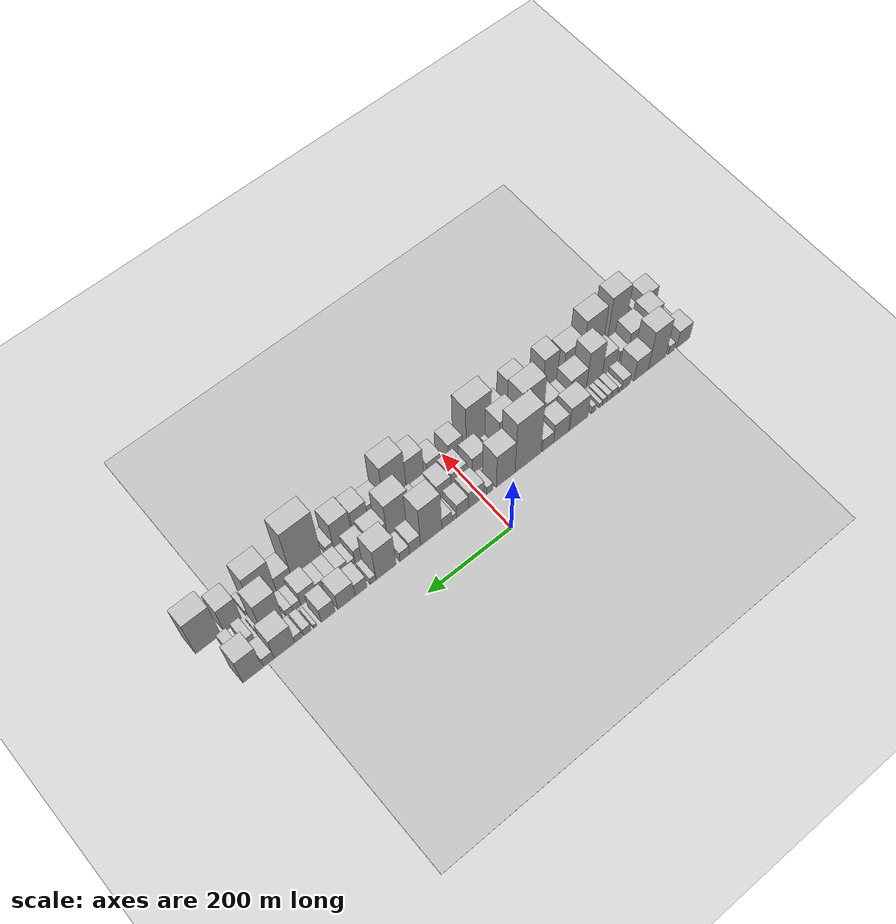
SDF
<?xml version="1.0" encoding="utf-8"?>

<sdf version="1.6">

   <world name="default">

      <gui fullscreen="0">

         <camera name="user_camera">

            <pose>-15 0 4.57585 0 0 0</pose>

            <view_controller>orbit</view_controller>

         </camera>

      </gui>

      <scene>

         <sky>

           <clouds>

             <speed>12</speed>

           </clouds>

         </sky>

         <ambient>0.4 0.4 0.4 1</ambient>

         <background>0.7 0.7 0.7 1</background>

         <shadows>1</shadows>

      </scene>

      <gravity>0 0 -9.8066</gravity>

      <magnetic_field>6e-06 2.3e-05 -4.2e-05</magnetic_field>

      <physics default="0" name="default_physics" type="ode">

         <ode>

            <solver>

               <type>quick</type>

               <iters>10</iters>

               <sor>1.0</sor>

               <use_dynamic_moi_rescaling>0</use_dynamic_moi_rescaling>

            </solver>

            <constraints>

               <cfm>0</cfm>

               <erp>0.2</erp>

               <contact_max_correcting_vel>100</contact_max_correcting_vel>

               <contact_surface_layer>0.001</contact_surface_layer>

            </constraints>

         </ode>

         <max_step_size>0.004</max_step_size>

         <real_time_factor>1</real_time_factor>

         <real_time_update_rate>250</real_time_update_rate>

      </physics>

      <light name="sun" type="directional">

         <cast_shadows>1</cast_shadows>

         <pose>0 0 10 0 0 0</pose>

         <diffuse>0.8 0.8 0.8 1</diffuse>

         <specular>0.2 0.2 0.2 1</specular>

         <attenuation>

            <range>1000</range>

            <constant>0.9</constant>

            <linear>0.01</linear>

            <quadratic>0.001</quadratic>

         </attenuation>

         <direction>-0.5 0.1 -0.9</direction>

      </light>

      <include>

         <name>ground_plane_1</name>

         <uri>model://HANNAS_ground_plane</uri>

         <pose>0 0 0  0 0 0</pose>

      </include>

      <include>

         <name>ground_plane_2</name>

         <uri>model://HANNAS_ground_plane</uri>

         <pose>100 0 0  0 0 0</pose>

      </include>

      <model name="building_1">

         <static>1</static>

         <pose frame="">100.0000 -518.3158 0 0.000000 0.000000 0.000000</pose>

         <link name="link">

            <pose frame="">0 0 30.00 0 0 0</pose>

            <collision name="collision">

               <geometry>

                  <box>

                     <size>40.0000 35.3684 60.0000</size>

                  </box>

               </geometry>

               <max_contacts>10</max_contacts>

               <surface>

                  <contact>

                     <ode/>

                  </contact>

                  <bounce/>

                  <friction>

                     <torsional>

                        <ode/>

                     </torsional>

                     <ode/>

                  </friction>

               </surface>

            </collision>

            <visual name="visual">

               <cast_shadows>0</cast_shadows>

               <geometry>

                  <box>

                     <size>40.0000 35.3684 60.0000</size>

                  </box>

               </geometry>

               <material>

                  <script>

                     <uri>model://HANNAS_wall/materials/scripts</uri>

                     <uri>model://HANNAS_wall/materials/textures</uri>

                     <name>vrc/HANNAS_wall</name>

                  </script>

               </material>

            </visual>

            <self_collide>0</self_collide>

            <enable_wind>0</enable_wind>

            <kinematic>0</kinematic>

         </link>

      </model>

      <model name="building_2">

         <static>1</static>

         <pose frame="">100.0000 -485.6401 0 0.000000 0.000000 0.000000</pose>

         <link name="link">

            <pose frame="">0 0 15.00 0 0 0</pose>

            <collision name="collision">

               <geometry>

                  <box>

                     <size>40.0000 15.9831 30.0000</size>

                  </box>

               </geometry>

               <max_contacts>10</max_contacts>

               <surface>

                  <contact>

                     <ode/>

                  </contact>

                  <bounce/>

                  <friction>

                     <torsional>

                        <ode/>

                     </torsional>

                     <ode/>

                  </friction>

               </surface>

            </collision>

            <visual name="visual">

               <cast_shadows>0</cast_shadows>

               <geometry>

                  <box>

                     <size>40.0000 15.9831 30.0000</size>

                  </box>

               </geometry>

               <material>

                  <script>

                     <uri>model://HANNAS_wall/materials/scripts</uri>

                     <uri>model://HANNAS_wall/materials/textures</uri>

                     <name>vrc/HANNAS_wall</name>

                  </script>

               </material>

            </visual>

            <self_collide>0</self_collide>

            <enable_wind>0</enable_wind>

            <kinematic>0</kinematic>

         </link>

      </model>

      <model name="building_3">

         <static>1</static>

         <pose frame="">100.0000 -447.0525 0 0.000000 0.000000 0.000000</pose>

         <link name="link">

            <pose frame="">0 0 69.00 0 0 0</pose>

            <collision name="collision">

               <geometry>

                  <box>

                     <size>40.0000 47.1920 138.0000</size>

                  </box>

               </geometry>

               <max_contacts>10</max_contacts>

               <surface>

                  <contact>

                     <ode/>

                  </contact>

                  <bounce/>

                  <friction>

                     <torsional>

                        <ode/>

                     </torsional>

                     <ode/>

                  </friction>

               </surface>

            </collision>

            <visual name="visual">

               <cast_shadows>0</cast_shadows>

               <geometry>

                  <box>

                     <size>40.0000 47.1920 138.0000</size>

                  </box>

               </geometry>

               <material>

                  <script>

                     <uri>model://HANNAS_wall/materials/scripts</uri>

                     <uri>model://HANNAS_wall/materials/textures</uri>

                     <name>vrc/HANNAS_wall</name>

                  </script>

               </material>

            </visual>

            <self_collide>0</self_collide>

            <enable_wind>0</enable_wind>

            <kinematic>0</kinematic>

         </link>

      </model>

      <model name="building_4">

         <static>1</static>

         <pose frame="">100.0000 -404.3314 0 0.000000 0.000000 0.000000</pose>

         <link name="link">

            <pose frame="">0 0 37.50 0 0 0</pose>

            <collision name="collision">

               <geometry>

                  <box>

                     <size>40.0000 38.2501 75.0000</size>

                  </box>

               </geometry>

               <max_contacts>10</max_contacts>

               <surface>

                  <contact>

                     <ode/>

                  </contact>

                  <bounce/>

                  <friction>

                     <torsional>

                        <ode/>

                     </torsional>

                     <ode/>

                  </friction>

               </surface>

            </collision>

            <visual name="visual">

               <cast_shadows>0</cast_shadows>

               <geometry>

                  <box>

                     <size>40.0000 38.2501 75.0000</size>

                  </box>

               </geometry>

               <material>

                  <script>

                     <uri>model://HANNAS_wall/materials/scripts</uri>

                     <uri>model://HANNAS_wall/materials/textures</uri>

                     <name>vrc/HANNAS_wall</name>

                  </script>

               </material>

            </visual>

            <self_collide>0</self_collide>

            <enable_wind>0</enable_wind>

            <kinematic>0</kinematic>

         </link>

      </model>

      <model name="building_5">

         <static>1</static>

         <pose frame="">100.0000 -364.0573 0 0.000000 0.000000 0.000000</pose>

         <link name="link">

            <pose frame="">0 0 19.50 0 0 0</pose>

            <collision name="collision">

               <geometry>

                  <box>

                     <size>40.0000 22.2982 39.0000</size>

                  </box>

               </geometry>

               <max_contacts>10</max_contacts>

               <surface>

                  <contact>

                     <ode/>

                  </contact>

                  <bounce/>

                  <friction>

                     <torsional>

                        <ode/>

                     </torsional>

                     <ode/>

                  </friction>

               </surface>

            </collision>

            <visual name="visual">

               <cast_shadows>0</cast_shadows>

               <geometry>

                  <box>

                     <size>40.0000 22.2982 39.0000</size>

                  </box>

               </geometry>

               <material>

                  <script>

                     <uri>model://HANNAS_wall/materials/scripts</uri>

                     <uri>model://HANNAS_wall/materials/textures</uri>

                     <name>vrc/HANNAS_wall</name>

                  </script>

               </material>

            </visual>

            <self_collide>0</self_collide>

            <enable_wind>0</enable_wind>

            <kinematic>0</kinematic>

         </link>

      </model>

      <model name="building_6">

         <static>1</static>

         <pose frame="">100.0000 -348.7024 0 0.000000 0.000000 0.000000</pose>

         <link name="link">

            <pose frame="">0 0 10.50 0 0 0</pose>

            <collision name="collision">

               <geometry>

                  <box>

                     <size>40.0000 8.4116 21.0000</size>

                  </box>

               </geometry>

               <max_contacts>10</max_contacts>

               <surface>

                  <contact>

                     <ode/>

                  </contact>

                  <bounce/>

                  <friction>

                     <torsional>

                        <ode/>

                     </torsional>

                     <ode/>

                  </friction>

               </surface>

            </collision>

            <visual name="visual">

               <cast_shadows>0</cast_shadows>

               <geometry>

                  <box>

                     <size>40.0000 8.4116 21.0000</size>

                  </box>

               </geometry>

               <material>

                  <script>

                     <uri>model://HANNAS_wall/materials/scripts</uri>

                     <uri>model://HANNAS_wall/materials/textures</uri>

                     <name>vrc/HANNAS_wall</name>

                  </script>

               </material>

            </visual>

            <self_collide>0</self_collide>

            <enable_wind>0</enable_wind>

            <kinematic>0</kinematic>

         </link>

      </model>

      <model name="building_7">

         <static>1</static>

         <pose frame="">100.0000 -333.5226 0 0.000000 0.000000 0.000000</pose>

         <link name="link">

            <pose frame="">0 0 15.00 0 0 0</pose>

            <collision name="collision">

               <geometry>

                  <box>

                     <size>40.0000 15.9480 30.0000</size>

                  </box>

               </geometry>

               <max_contacts>10</max_contacts>

               <surface>

                  <contact>

                     <ode/>

                  </contact>

                  <bounce/>

                  <friction>

                     <torsional>

                        <ode/>

                     </torsional>

                     <ode/>

                  </friction>

               </surface>

            </collision>

            <visual name="visual">

               <cast_shadows>0</cast_shadows>

               <geometry>

                  <box>

                     <size>40.0000 15.9480 30.0000</size>

                  </box>

               </geometry>

               <material>

                  <script>

                     <uri>model://HANNAS_wall/materials/scripts</uri>

                     <uri>model://HANNAS_wall/materials/textures</uri>

                     <name>vrc/HANNAS_wall</name>

                  </script>

               </material>

            </visual>

            <self_collide>0</self_collide>

            <enable_wind>0</enable_wind>

            <kinematic>0</kinematic>

         </link>

      </model>

      <model name="building_8">

         <static>1</static>

         <pose frame="">100.0000 -319.4158 0 0.000000 0.000000 0.000000</pose>

         <link name="link">

            <pose frame="">0 0 13.50 0 0 0</pose>

            <collision name="collision">

               <geometry>

                  <box>

                     <size>40.0000 12.2657 27.0000</size>

                  </box>

               </geometry>

               <max_contacts>10</max_contacts>

               <surface>

                  <contact>

                     <ode/>

                  </contact>

                  <bounce/>

                  <friction>

                     <torsional>

                        <ode/>

                     </torsional>

                     <ode/>

                  </friction>

               </surface>

            </collision>

            <visual name="visual">

               <cast_shadows>0</cast_shadows>

               <geometry>

                  <box>

                     <size>40.0000 12.2657 27.0000</size>

                  </box>

               </geometry>

               <material>

                  <script>

                     <uri>model://HANNAS_wall/materials/scripts</uri>

                     <uri>model://HANNAS_wall/materials/textures</uri>

                     <name>vrc/HANNAS_wall</name>

                  </script>

               </material>

            </visual>

            <self_collide>0</self_collide>

            <enable_wind>0</enable_wind>

            <kinematic>0</kinematic>

         </link>

      </model>

      <model name="building_9">

         <static>1</static>

         <pose frame="">100.0000 -307.5187 0 0.000000 0.000000 0.000000</pose>

         <link name="link">

            <pose frame="">0 0 12.00 0 0 0</pose>

            <collision name="collision">

               <geometry>

                  <box>

                     <size>40.0000 11.5283 24.0000</size>

                  </box>

               </geometry>

               <max_contacts>10</max_contacts>

               <surface>

                  <contact>

                     <ode/>

                  </contact>

                  <bounce/>

                  <friction>

                     <torsional>

                        <ode/>

                     </torsional>

                     <ode/>

                  </friction>

               </surface>

            </collision>

            <visual name="visual">

               <cast_shadows>0</cast_shadows>

               <geometry>

                  <box>

                     <size>40.0000 11.5283 24.0000</size>

                  </box>

               </geometry>

               <material>

                  <script>

                     <uri>model://HANNAS_wall/materials/scripts</uri>

                     <uri>model://HANNAS_wall/materials/textures</uri>

                     <name>vrc/HANNAS_wall</name>

                  </script>

               </material>

            </visual>

            <self_collide>0</self_collide>

            <enable_wind>0</enable_wind>

            <kinematic>0</kinematic>

         </link>

      </model>

      <model name="building_10">

         <static>1</static>

         <pose frame="">100.0000 -297.6573 0 0.000000 0.000000 0.000000</pose>

         <link name="link">

            <pose frame="">0 0 9.00 0 0 0</pose>

            <collision name="collision">

               <geometry>

                  <box>

                     <size>40.0000 8.1947 18.0000</size>

                  </box>

               </geometry>

               <max_contacts>10</max_contacts>

               <surface>

                  <contact>

                     <ode/>

                  </contact>

                  <bounce/>

                  <friction>

                     <torsional>

                        <ode/>

                     </torsional>

                     <ode/>

                  </friction>

               </surface>

            </collision>

            <visual name="visual">

               <cast_shadows>0</cast_shadows>

               <geometry>

                  <box>

                     <size>40.0000 8.1947 18.0000</size>

                  </box>

               </geometry>

               <material>

                  <script>

                     <uri>model://HANNAS_wall/materials/scripts</uri>

                     <uri>model://HANNAS_wall/materials/textures</uri>

                     <name>vrc/HANNAS_wall</name>

                  </script>

               </material>

            </visual>

            <self_collide>0</self_collide>

            <enable_wind>0</enable_wind>

            <kinematic>0</kinematic>

         </link>

      </model>

      <model name="building_11">

         <static>1</static>

         <pose frame="">100.0000 -278.9061 0 0.000000 0.000000 0.000000</pose>

         <link name="link">

            <pose frame="">0 0 13.50 0 0 0</pose>

            <collision name="collision">

               <geometry>

                  <box>

                     <size>40.0000 11.3076 27.0000</size>

                  </box>

               </geometry>

               <max_contacts>10</max_contacts>

               <surface>

                  <contact>

                     <ode/>

                  </contact>

                  <bounce/>

                  <friction>

                     <torsional>

                        <ode/>

                     </torsional>

                     <ode/>

                  </friction>

               </surface>

            </collision>

            <visual name="visual">

               <cast_shadows>0</cast_shadows>

               <geometry>

                  <box>

                     <size>40.0000 11.3076 27.0000</size>

                  </box>

               </geometry>

               <material>

                  <script>

                     <uri>model://HANNAS_wall/materials/scripts</uri>

                     <uri>model://HANNAS_wall/materials/textures</uri>

                     <name>vrc/HANNAS_wall</name>

                  </script>

               </material>

            </visual>

            <self_collide>0</self_collide>

            <enable_wind>0</enable_wind>

            <kinematic>0</kinematic>

         </link>

      </model>

      <model name="building_12">

         <static>1</static>

         <pose frame="">100.0000 -240.6720 0 0.000000 0.000000 0.000000</pose>

         <link name="link">

            <pose frame="">0 0 43.50 0 0 0</pose>

            <collision name="collision">

               <geometry>

                  <box>

                     <size>40.0000 47.1606 87.0000</size>

                  </box>

               </geometry>

               <max_contacts>10</max_contacts>

               <surface>

                  <contact>

                     <ode/>

                  </contact>

                  <bounce/>

                  <friction>

                     <torsional>

                        <ode/>

                     </torsional>

                     <ode/>

                  </friction>

               </surface>

            </collision>

            <visual name="visual">

               <cast_shadows>0</cast_shadows>

               <geometry>

                  <box>

                     <size>40.0000 47.1606 87.0000</size>

                  </box>

               </geometry>

               <material>

                  <script>

                     <uri>model://HANNAS_wall/materials/scripts</uri>

                     <uri>model://HANNAS_wall/materials/textures</uri>

                     <name>vrc/HANNAS_wall</name>

                  </script>

               </material>

            </visual>

            <self_collide>0</self_collide>

            <enable_wind>0</enable_wind>

            <kinematic>0</kinematic>

         </link>

      </model>

      <model name="building_13">

         <static>1</static>

         <pose frame="">100.0000 -195.0961 0 0.000000 0.000000 0.000000</pose>

         <link name="link">

            <pose frame="">0 0 36.00 0 0 0</pose>

            <collision name="collision">

               <geometry>

                  <box>

                     <size>40.0000 37.9914 72.0000</size>

                  </box>

               </geometry>

               <max_contacts>10</max_contacts>

               <surface>

                  <contact>

                     <ode/>

                  </contact>

                  <bounce/>

                  <friction>

                     <torsional>

                        <ode/>

                     </torsional>

                     <ode/>

                  </friction>

               </surface>

            </collision>

            <visual name="visual">

               <cast_shadows>0</cast_shadows>

               <geometry>

                  <box>

                     <size>40.0000 37.9914 72.0000</size>

                  </box>

               </geometry>

               <material>

                  <script>

                     <uri>model://HANNAS_wall/materials/scripts</uri>

                     <uri>model://HANNAS_wall/materials/textures</uri>

                     <name>vrc/HANNAS_wall</name>

                  </script>

               </material>

            </visual>

            <self_collide>0</self_collide>

            <enable_wind>0</enable_wind>

            <kinematic>0</kinematic>

         </link>

      </model>

      <model name="building_14">

         <static>1</static>

         <pose frame="">100.0000 -161.9064 0 0.000000 0.000000 0.000000</pose>

         <link name="link">

            <pose frame="">0 0 24.00 0 0 0</pose>

            <collision name="collision">

               <geometry>

                  <box>

                     <size>40.0000 28.3878 48.0000</size>

                  </box>

               </geometry>

               <max_contacts>10</max_contacts>

               <surface>

                  <contact>

                     <ode/>

                  </contact>

                  <bounce/>

                  <friction>

                     <torsional>

                        <ode/>

                     </torsional>

                     <ode/>

                  </friction>

               </surface>

            </collision>

            <visual name="visual">

               <cast_shadows>0</cast_shadows>

               <geometry>

                  <box>

                     <size>40.0000 28.3878 48.0000</size>

                  </box>

               </geometry>

               <material>

                  <script>

                     <uri>model://HANNAS_wall/materials/scripts</uri>

                     <uri>model://HANNAS_wall/materials/textures</uri>

                     <name>vrc/HANNAS_wall</name>

                  </script>

               </material>

            </visual>

            <self_collide>0</self_collide>

            <enable_wind>0</enable_wind>

            <kinematic>0</kinematic>

         </link>

      </model>

      <model name="building_15">

         <static>1</static>

         <pose frame="">100.0000 -111.3881 0 0.000000 0.000000 0.000000</pose>

         <link name="link">

            <pose frame="">0 0 97.50 0 0 0</pose>

            <collision name="collision">

               <geometry>

                  <box>

                     <size>40.0000 64.6489 195.0000</size>

                  </box>

               </geometry>

               <max_contacts>10</max_contacts>

               <surface>

                  <contact>

                     <ode/>

                  </contact>

                  <bounce/>

                  <friction>

                     <torsional>

                        <ode/>

                     </torsional>

                     <ode/>

                  </friction>

               </surface>

            </collision>

            <visual name="visual">

               <cast_shadows>0</cast_shadows>

               <geometry>

                  <box>

                     <size>40.0000 64.6489 195.0000</size>

                  </box>

               </geometry>

               <material>

                  <script>

                     <uri>model://HANNAS_wall/materials/scripts</uri>

                     <uri>model://HANNAS_wall/materials/textures</uri>

                     <name>vrc/HANNAS_wall</name>

                  </script>

               </material>

            </visual>

            <self_collide>0</self_collide>

            <enable_wind>0</enable_wind>

            <kinematic>0</kinematic>

         </link>

      </model>

      <model name="building_16">

         <static>1</static>

         <pose frame="">100.0000 -55.8032 0 0.000000 0.000000 0.000000</pose>

         <link name="link">

            <pose frame="">0 0 63.00 0 0 0</pose>

            <collision name="collision">

               <geometry>

                  <box>

                     <size>40.0000 46.5208 126.0000</size>

                  </box>

               </geometry>

               <max_contacts>10</max_contacts>

               <surface>

                  <contact>

                     <ode/>

                  </contact>

                  <bounce/>

                  <friction>

                     <torsional>

                        <ode/>

                     </torsional>

                     <ode/>

                  </friction>

               </surface>

            </collision>

            <visual name="visual">

               <cast_shadows>0</cast_shadows>

               <geometry>

                  <box>

                     <size>40.0000 46.5208 126.0000</size>

                  </box>

               </geometry>

               <material>

                  <script>

                     <uri>model://HANNAS_wall/materials/scripts</uri>

                     <uri>model://HANNAS_wall/materials/textures</uri>

                     <name>vrc/HANNAS_wall</name>

                  </script>

               </material>

            </visual>

            <self_collide>0</self_collide>

            <enable_wind>0</enable_wind>

            <kinematic>0</kinematic>

         </link>

      </model>

      <model name="building_17">

         <static>1</static>

         <pose frame="">100.0000 -16.9928 0 0.000000 0.000000 0.000000</pose>

         <link name="link">

            <pose frame="">0 0 15.00 0 0 0</pose>

            <collision name="collision">

               <geometry>

                  <box>

                     <size>40.0000 15.0999 30.0000</size>

                  </box>

               </geometry>

               <max_contacts>10</max_contacts>

               <surface>

                  <contact>

                     <ode/>

                  </contact>

                  <bounce/>

                  <friction>

                     <torsional>

                        <ode/>

                     </torsional>

                     <ode/>

                  </friction>

               </surface>

            </collision>

            <visual name="visual">

               <cast_shadows>0</cast_shadows>

               <geometry>

                  <box>

                     <size>40.0000 15.0999 30.0000</size>

                  </box>

               </geometry>

               <material>

                  <script>

                     <uri>model://HANNAS_wall/materials/scripts</uri>

                     <uri>model://HANNAS_wall/materials/textures</uri>

                     <name>vrc/HANNAS_wall</name>

                  </script>

               </material>

            </visual>

            <self_collide>0</self_collide>

            <enable_wind>0</enable_wind>

            <kinematic>0</kinematic>

         </link>

      </model>

      <model name="building_18">

         <static>1</static>

         <pose frame="">100.0000 16.3628 0 0.000000 0.000000 0.000000</pose>

         <link name="link">

            <pose frame="">0 0 33.00 0 0 0</pose>

            <collision name="collision">

               <geometry>

                  <box>

                     <size>40.0000 37.6113 66.0000</size>

                  </box>

               </geometry>

               <max_contacts>10</max_contacts>

               <surface>

                  <contact>

                     <ode/>

                  </contact>

                  <bounce/>

                  <friction>

                     <torsional>

                        <ode/>

                     </torsional>

                     <ode/>

                  </friction>

               </surface>

            </collision>

            <visual name="visual">

               <cast_shadows>0</cast_shadows>

               <geometry>

                  <box>

                     <size>40.0000 37.6113 66.0000</size>

                  </box>

               </geometry>

               <material>

                  <script>

                     <uri>model://HANNAS_wall/materials/scripts</uri>

                     <uri>model://HANNAS_wall/materials/textures</uri>

                     <name>vrc/HANNAS_wall</name>

                  </script>

               </material>

            </visual>

            <self_collide>0</self_collide>

            <enable_wind>0</enable_wind>

            <kinematic>0</kinematic>

         </link>

      </model>

      <model name="building_19">

         <static>1</static>

         <pose frame="">100.0000 49.8645 0 0.000000 0.000000 0.000000</pose>

         <link name="link">

            <pose frame="">0 0 27.00 0 0 0</pose>

            <collision name="collision">

               <geometry>

                  <box>

                     <size>40.0000 29.3922 54.0000</size>

                  </box>

               </geometry>

               <max_contacts>10</max_contacts>

               <surface>

                  <contact>

                     <ode/>

                  </contact>

                  <bounce/>

                  <friction>

                     <torsional>

                        <ode/>

                     </torsional>

                     <ode/>

                  </friction>

               </surface>

            </collision>

            <visual name="visual">

               <cast_shadows>0</cast_shadows>

               <geometry>

                  <box>

                     <size>40.0000 29.3922 54.0000</size>

                  </box>

               </geometry>

               <material>

                  <script>

                     <uri>model://HANNAS_wall/materials/scripts</uri>

                     <uri>model://HANNAS_wall/materials/textures</uri>

                     <name>vrc/HANNAS_wall</name>

                  </script>

               </material>

            </visual>

            <self_collide>0</self_collide>

            <enable_wind>0</enable_wind>

            <kinematic>0</kinematic>

         </link>

      </model>

      <model name="building_20">

         <static>1</static>

         <pose frame="">100.0000 69.6994 0 0.000000 0.000000 0.000000</pose>

         <link name="link">

            <pose frame="">0 0 12.00 0 0 0</pose>

            <collision name="collision">

               <geometry>

                  <box>

                     <size>40.0000 10.2777 24.0000</size>

                  </box>

               </geometry>

               <max_contacts>10</max_contacts>

               <surface>

                  <contact>

                     <ode/>

                  </contact>

                  <bounce/>

                  <friction>

                     <torsional>

                        <ode/>

                     </torsional>

                     <ode/>

                  </friction>

               </surface>

            </collision>

            <visual name="visual">

               <cast_shadows>0</cast_shadows>

               <geometry>

                  <box>

                     <size>40.0000 10.2777 24.0000</size>

                  </box>

               </geometry>

               <material>

                  <script>

                     <uri>model://HANNAS_wall/materials/scripts</uri>

                     <uri>model://HANNAS_wall/materials/textures</uri>

                     <name>vrc/HANNAS_wall</name>

                  </script>

               </material>

            </visual>

            <self_collide>0</self_collide>

            <enable_wind>0</enable_wind>

            <kinematic>0</kinematic>

         </link>

      </model>

      <model name="building_21">

         <static>1</static>

         <pose frame="">100.0000 87.3972 0 0.000000 0.000000 0.000000</pose>

         <link name="link">

            <pose frame="">0 0 22.50 0 0 0</pose>

            <collision name="collision">

               <geometry>

                  <box>

                     <size>40.0000 25.1180 45.0000</size>

                  </box>

               </geometry>

               <max_contacts>10</max_contacts>

               <surface>

                  <contact>

                     <ode/>

                  </contact>

                  <bounce/>

                  <friction>

                     <torsional>

                        <ode/>

                     </torsional>

                     <ode/>

                  </friction>

               </surface>

            </collision>

            <visual name="visual">

               <cast_shadows>0</cast_shadows>

               <geometry>

                  <box>

                     <size>40.0000 25.1180 45.0000</size>

                  </box>

               </geometry>

               <material>

                  <script>

                     <uri>model://HANNAS_wall/materials/scripts</uri>

                     <uri>model://HANNAS_wall/materials/textures</uri>

                     <name>vrc/HANNAS_wall</name>

                  </script>

               </material>

            </visual>

            <self_collide>0</self_collide>

            <enable_wind>0</enable_wind>

            <kinematic>0</kinematic>

         </link>

      </model>

      <model name="building_22">

         <static>1</static>

         <pose frame="">100.0000 125.3921 0 0.000000 0.000000 0.000000</pose>

         <link name="link">

            <pose frame="">0 0 78.00 0 0 0</pose>

            <collision name="collision">

               <geometry>

                  <box>

                     <size>40.0000 50.8718 156.0000</size>

                  </box>

               </geometry>

               <max_contacts>10</max_contacts>

               <surface>

                  <contact>

                     <ode/>

                  </contact>

                  <bounce/>

                  <friction>

                     <torsional>

                        <ode/>

                     </torsional>

                     <ode/>

                  </friction>

               </surface>

            </collision>

            <visual name="visual">

               <cast_shadows>0</cast_shadows>

               <geometry>

                  <box>

                     <size>40.0000 50.8718 156.0000</size>

                  </box>

               </geometry>

               <material>

                  <script>

                     <uri>model://HANNAS_wall/materials/scripts</uri>

                     <uri>model://HANNAS_wall/materials/textures</uri>

                     <name>vrc/HANNAS_wall</name>

                  </script>

               </material>

            </visual>

            <self_collide>0</self_collide>

            <enable_wind>0</enable_wind>

            <kinematic>0</kinematic>

         </link>

      </model>

      <model name="building_23">

         <static>1</static>

         <pose frame="">100.0000 163.8808 0 0.000000 0.000000 0.000000</pose>

         <link name="link">

            <pose frame="">0 0 25.50 0 0 0</pose>

            <collision name="collision">

               <geometry>

                  <box>

                     <size>40.0000 26.1055 51.0000</size>

                  </box>

               </geometry>

               <max_contacts>10</max_contacts>

               <surface>

                  <contact>

                     <ode/>

                  </contact>

                  <bounce/>

                  <friction>

                     <torsional>

                        <ode/>

                     </torsional>

                     <ode/>

                  </friction>

               </surface>

            </collision>

            <visual name="visual">

               <cast_shadows>0</cast_shadows>

               <geometry>

                  <box>

                     <size>40.0000 26.1055 51.0000</size>

                  </box>

               </geometry>

               <material>

                  <script>

                     <uri>model://HANNAS_wall/materials/scripts</uri>

                     <uri>model://HANNAS_wall/materials/textures</uri>

                     <name>vrc/HANNAS_wall</name>

                  </script>

               </material>

            </visual>

            <self_collide>0</self_collide>

            <enable_wind>0</enable_wind>

            <kinematic>0</kinematic>

         </link>

      </model>

      <model name="building_24">

         <static>1</static>

         <pose frame="">100.0000 188.3058 0 0.000000 0.000000 0.000000</pose>

         <link name="link">

            <pose frame="">0 0 19.50 0 0 0</pose>

            <collision name="collision">

               <geometry>

                  <box>

                     <size>40.0000 22.7445 39.0000</size>

                  </box>

               </geometry>

               <max_contacts>10</max_contacts>

               <surface>

                  <contact>

                     <ode/>

                  </contact>

                  <bounce/>

                  <friction>

                     <torsional>

                        <ode/>

                     </torsional>

                     <ode/>

                  </friction>

               </surface>

            </collision>

            <visual name="visual">

               <cast_shadows>0</cast_shadows>

               <geometry>

                  <box>

                     <size>40.0000 22.7445 39.0000</size>

                  </box>

               </geometry>

               <material>

                  <script>

                     <uri>model://HANNAS_wall/materials/scripts</uri>

                     <uri>model://HANNAS_wall/materials/textures</uri>

                     <name>vrc/HANNAS_wall</name>

                  </script>

               </material>

            </visual>

            <self_collide>0</self_collide>

            <enable_wind>0</enable_wind>

            <kinematic>0</kinematic>

         </link>

      </model>

      <model name="building_25">

         <static>1</static>

         <pose frame="">100.0000 232.1105 0 0.000000 0.000000 0.000000</pose>

         <link name="link">

            <pose frame="">0 0 64.50 0 0 0</pose>

            <collision name="collision">

               <geometry>

                  <box>

                     <size>40.0000 46.8650 129.0000</size>

                  </box>

               </geometry>

               <max_contacts>10</max_contacts>

               <surface>

                  <contact>

                     <ode/>

                  </contact>

                  <bounce/>

                  <friction>

                     <torsional>

                        <ode/>

                     </torsional>

                     <ode/>

                  </friction>

               </surface>

            </collision>

            <visual name="visual">

               <cast_shadows>0</cast_shadows>

               <geometry>

                  <box>

                     <size>40.0000 46.8650 129.0000</size>

                  </box>

               </geometry>

               <material>

                  <script>

                     <uri>model://HANNAS_wall/materials/scripts</uri>

                     <uri>model://HANNAS_wall/materials/textures</uri>

                     <name>vrc/HANNAS_wall</name>

                  </script>

               </material>

            </visual>

            <self_collide>0</self_collide>

            <enable_wind>0</enable_wind>

            <kinematic>0</kinematic>

         </link>

      </model>

      <model name="building_26">

         <static>1</static>

         <pose frame="">100.0000 262.1391 0 0.000000 0.000000 0.000000</pose>

         <link name="link">

            <pose frame="">0 0 13.50 0 0 0</pose>

            <collision name="collision">

               <geometry>

                  <box>

                     <size>40.0000 13.1922 27.0000</size>

                  </box>

               </geometry>

               <max_contacts>10</max_contacts>

               <surface>

                  <contact>

                     <ode/>

                  </contact>

                  <bounce/>

                  <friction>

                     <torsional>

                        <ode/>

                     </torsional>

                     <ode/>

                  </friction>

               </surface>

            </collision>

            <visual name="visual">

               <cast_shadows>0</cast_shadows>

               <geometry>

                  <box>

                     <size>40.0000 13.1922 27.0000</size>

                  </box>

               </geometry>

               <material>

                  <script>

                     <uri>model://HANNAS_wall/materials/scripts</uri>

                     <uri>model://HANNAS_wall/materials/textures</uri>

                     <name>vrc/HANNAS_wall</name>

                  </script>

               </material>

            </visual>

            <self_collide>0</self_collide>

            <enable_wind>0</enable_wind>

            <kinematic>0</kinematic>

         </link>

      </model>

      <model name="building_27">

         <static>1</static>

         <pose frame="">100.0000 290.3768 0 0.000000 0.000000 0.000000</pose>

         <link name="link">

            <pose frame="">0 0 25.50 0 0 0</pose>

            <collision name="collision">

               <geometry>

                  <box>

                     <size>40.0000 27.2832 51.0000</size>

                  </box>

               </geometry>

               <max_contacts>10</max_contacts>

               <surface>

                  <contact>

                     <ode/>

                  </contact>

                  <bounce/>

                  <friction>

                     <torsional>

                        <ode/>

                     </torsional>

                     <ode/>

                  </friction>

               </surface>

            </collision>

            <visual name="visual">

               <cast_shadows>0</cast_shadows>

               <geometry>

                  <box>

                     <size>40.0000 27.2832 51.0000</size>

                  </box>

               </geometry>

               <material>

                  <script>

                     <uri>model://HANNAS_wall/materials/scripts</uri>

                     <uri>model://HANNAS_wall/materials/textures</uri>

                     <name>vrc/HANNAS_wall</name>

                  </script>

               </material>

            </visual>

            <self_collide>0</self_collide>

            <enable_wind>0</enable_wind>

            <kinematic>0</kinematic>

         </link>

      </model>

      <model name="building_28">

         <static>1</static>

         <pose frame="">100.0000 323.7900 0 0.000000 0.000000 0.000000</pose>

         <link name="link">

            <pose frame="">0 0 34.50 0 0 0</pose>

            <collision name="collision">

               <geometry>

                  <box>

                     <size>40.0000 39.5433 69.0000</size>

                  </box>

               </geometry>

               <max_contacts>10</max_contacts>

               <surface>

                  <contact>

                     <ode/>

                  </contact>

                  <bounce/>

                  <friction>

                     <torsional>

                        <ode/>

                     </torsional>

                     <ode/>

                  </friction>

               </surface>

            </collision>

            <visual name="visual">

               <cast_shadows>0</cast_shadows>

               <geometry>

                  <box>

                     <size>40.0000 39.5433 69.0000</size>

                  </box>

               </geometry>

               <material>

                  <script>

                     <uri>model://HANNAS_wall/materials/scripts</uri>

                     <uri>model://HANNAS_wall/materials/textures</uri>

                     <name>vrc/HANNAS_wall</name>

                  </script>

               </material>

            </visual>

            <self_collide>0</self_collide>

            <enable_wind>0</enable_wind>

            <kinematic>0</kinematic>

         </link>

      </model>

      <model name="building_29">

         <static>1</static>

         <pose frame="">100.0000 365.4495 0 0.000000 0.000000 0.000000</pose>

         <link name="link">

            <pose frame="">0 0 30.00 0 0 0</pose>

            <collision name="collision">

               <geometry>

                  <box>

                     <size>40.0000 31.7757 60.0000</size>

                  </box>

               </geometry>

               <max_contacts>10</max_contacts>

               <surface>

                  <contact>

                     <ode/>

                  </contact>

                  <bounce/>

                  <friction>

                     <torsional>

                        <ode/>

                     </torsional>

                     <ode/>

                  </friction>

               </surface>

            </collision>

            <visual name="visual">

               <cast_shadows>0</cast_shadows>

               <geometry>

                  <box>

                     <size>40.0000 31.7757 60.0000</size>

                  </box>

               </geometry>

               <material>

                  <script>

                     <uri>model://HANNAS_wall/materials/scripts</uri>

                     <uri>model://HANNAS_wall/materials/textures</uri>

                     <name>vrc/HANNAS_wall</name>

                  </script>

               </material>

            </visual>

            <self_collide>0</self_collide>

            <enable_wind>0</enable_wind>

            <kinematic>0</kinematic>

         </link>

      </model>

      <model name="building_30">

         <static>1</static>

         <pose frame="">100.0000 395.0855 0 0.000000 0.000000 0.000000</pose>

         <link name="link">

            <pose frame="">0 0 7.50 0 0 0</pose>

            <collision name="collision">

               <geometry>

                  <box>

                     <size>40.0000 7.4964 15.0000</size>

                  </box>

               </geometry>

               <max_contacts>10</max_contacts>

               <surface>

                  <contact>

                     <ode/>

                  </contact>

                  <bounce/>

                  <friction>

                     <torsional>

                        <ode/>

                     </torsional>

                     <ode/>

                  </friction>

               </surface>

            </collision>

            <visual name="visual">

               <cast_shadows>0</cast_shadows>

               <geometry>

                  <box>

                     <size>40.0000 7.4964 15.0000</size>

                  </box>

               </geometry>

               <material>

                  <script>

                     <uri>model://HANNAS_wall/materials/scripts</uri>

                     <uri>model://HANNAS_wall/materials/textures</uri>

                     <name>vrc/HANNAS_wall</name>

                  </script>

               </material>

            </visual>

            <self_collide>0</self_collide>

            <enable_wind>0</enable_wind>

            <kinematic>0</kinematic>

         </link>

      </model>

      <model name="building_31">

         <static>1</static>

         <pose frame="">100.0000 412.2451 0 0.000000 0.000000 0.000000</pose>

         <link name="link">

            <pose frame="">0 0 15.00 0 0 0</pose>

            <collision name="collision">

               <geometry>

                  <box>

                     <size>40.0000 16.8228 30.0000</size>

                  </box>

               </geometry>

               <max_contacts>10</max_contacts>

               <surface>

                  <contact>

                     <ode/>

                  </contact>

                  <bounce/>

                  <friction>

                     <torsional>

                        <ode/>

                     </torsional>

                     <ode/>

                  </friction>

               </surface>

            </collision>

            <visual name="visual">

               <cast_shadows>0</cast_shadows>

               <geometry>

                  <box>

                     <size>40.0000 16.8228 30.0000</size>

                  </box>

               </geometry>

               <material>

                  <script>

                     <uri>model://HANNAS_wall/materials/scripts</uri>

                     <uri>model://HANNAS_wall/materials/textures</uri>

                     <name>vrc/HANNAS_wall</name>

                  </script>

               </material>

            </visual>

            <self_collide>0</self_collide>

            <enable_wind>0</enable_wind>

            <kinematic>0</kinematic>

         </link>

      </model>

      <model name="building_32">

         <static>1</static>

         <pose frame="">100.0000 432.3515 0 0.000000 0.000000 0.000000</pose>

         <link name="link">

            <pose frame="">0 0 15.00 0 0 0</pose>

            <collision name="collision">

               <geometry>

                  <box>

                     <size>40.0000 17.3901 30.0000</size>

                  </box>

               </geometry>

               <max_contacts>10</max_contacts>

               <surface>

                  <contact>

                     <ode/>

                  </contact>

                  <bounce/>

                  <friction>

                     <torsional>

                        <ode/>

                     </torsional>

                     <ode/>

                  </friction>

               </surface>

            </collision>

            <visual name="visual">

               <cast_shadows>0</cast_shadows>

               <geometry>

                  <box>

                     <size>40.0000 17.3901 30.0000</size>

                  </box>

               </geometry>

               <material>

                  <script>

                     <uri>model://HANNAS_wall/materials/scripts</uri>

                     <uri>model://HANNAS_wall/materials/textures</uri>

                     <name>vrc/HANNAS_wall</name>

                  </script>

               </material>

            </visual>

            <self_collide>0</self_collide>

            <enable_wind>0</enable_wind>

            <kinematic>0</kinematic>

         </link>

      </model>

      <model name="building_33">

         <static>1</static>

         <pose frame="">100.0000 463.8731 0 0.000000 0.000000 0.000000</pose>

         <link name="link">

            <pose frame="">0 0 45.00 0 0 0</pose>

            <collision name="collision">

               <geometry>

                  <box>

                     <size>40.0000 45.6530 90.0000</size>

                  </box>

               </geometry>

               <max_contacts>10</max_contacts>

               <surface>

                  <contact>

                     <ode/>

                  </contact>

                  <bounce/>

                  <friction>

                     <torsional>

                        <ode/>

                     </torsional>

                     <ode/>

                  </friction>

               </surface>

            </collision>

            <visual name="visual">

               <cast_shadows>0</cast_shadows>

               <geometry>

                  <box>

                     <size>40.0000 45.6530 90.0000</size>

                  </box>

               </geometry>

               <material>

                  <script>

                     <uri>model://HANNAS_wall/materials/scripts</uri>

                     <uri>model://HANNAS_wall/materials/textures</uri>

                     <name>vrc/HANNAS_wall</name>

                  </script>

               </material>

            </visual>

            <self_collide>0</self_collide>

            <enable_wind>0</enable_wind>

            <kinematic>0</kinematic>

         </link>

      </model>

      <model name="building_34">

         <static>1</static>

         <pose frame="">100.0000 498.3112 0 0.000000 0.000000 0.000000</pose>

         <link name="link">

            <pose frame="">0 0 19.50 0 0 0</pose>

            <collision name="collision">

               <geometry>

                  <box>

                     <size>40.0000 23.2232 39.0000</size>

                  </box>

               </geometry>

               <max_contacts>10</max_contacts>

               <surface>

                  <contact>

                     <ode/>

                  </contact>

                  <bounce/>

                  <friction>

                     <torsional>

                        <ode/>

                     </torsional>

                     <ode/>

                  </friction>

               </surface>

            </collision>

            <visual name="visual">

               <cast_shadows>0</cast_shadows>

               <geometry>

                  <box>

                     <size>40.0000 23.2232 39.0000</size>

                  </box>

               </geometry>

               <material>

                  <script>

                     <uri>model://HANNAS_wall/materials/scripts</uri>

                     <uri>model://HANNAS_wall/materials/textures</uri>

                     <name>vrc/HANNAS_wall</name>

                  </script>

               </material>

            </visual>

            <self_collide>0</self_collide>

            <enable_wind>0</enable_wind>

            <kinematic>0</kinematic>

         </link>

      </model>

      <model name="building_35">

         <static>1</static>

         <pose frame="">100.0000 534.2244 0 0.000000 0.000000 0.000000</pose>

         <link name="link">

            <pose frame="">0 0 54.00 0 0 0</pose>

            <collision name="collision">

               <geometry>

                  <box>

                     <size>40.0000 42.6031 108.0000</size>

                  </box>

               </geometry>

               <max_contacts>10</max_contacts>

               <surface>

                  <contact>

                     <ode/>

                  </contact>

                  <bounce/>

                  <friction>

                     <torsional>

                        <ode/>

                     </torsional>

                     <ode/>

                  </friction>

               </surface>

            </collision>

            <visual name="visual">

               <cast_shadows>0</cast_shadows>

               <geometry>

                  <box>

                     <size>40.0000 42.6031 108.0000</size>

                  </box>

               </geometry>

               <material>

                  <script>

                     <uri>model://HANNAS_wall/materials/scripts</uri>

                     <uri>model://HANNAS_wall/materials/textures</uri>

                     <name>vrc/HANNAS_wall</name>

                  </script>

               </material>

            </visual>

            <self_collide>0</self_collide>

            <enable_wind>0</enable_wind>

            <kinematic>0</kinematic>

         </link>

      </model>

      <model name="building_36">

         <static>1</static>

         <pose frame="">149.0000 -530.9297 0 0.000000 0.000000 0.000000</pose>

         <link name="link">

            <pose frame="">0 0 12.00 0 0 0</pose>

            <collision name="collision">

               <geometry>

                  <box>

                     <size>40.0000 10.1405 24.0000</size>

                  </box>

               </geometry>

               <max_contacts>10</max_contacts>

               <surface>

                  <contact>

                     <ode/>

                  </contact>

                  <bounce/>

                  <friction>

                     <torsional>

                        <ode/>

                     </torsional>

                     <ode/>

                  </friction>

               </surface>

            </collision>

            <visual name="visual">

               <cast_shadows>0</cast_shadows>

               <geometry>

                  <box>

                     <size>40.0000 10.1405 24.0000</size>

                  </box>

               </geometry>

               <material>

                  <script>

                     <uri>model://HANNAS_wall/materials/scripts</uri>

                     <uri>model://HANNAS_wall/materials/textures</uri>

                     <name>vrc/HANNAS_wall</name>

                  </script>

               </material>

            </visual>

            <self_collide>0</self_collide>

            <enable_wind>0</enable_wind>

            <kinematic>0</kinematic>

         </link>

      </model>

      <model name="building_37">

         <static>1</static>

         <pose frame="">149.0000 -522.1715 0 0.000000 0.000000 0.000000</pose>

         <link name="link">

            <pose frame="">0 0 9.00 0 0 0</pose>

            <collision name="collision">

               <geometry>

                  <box>

                     <size>40.0000 7.3759 18.0000</size>

                  </box>

               </geometry>

               <max_contacts>10</max_contacts>

               <surface>

                  <contact>

                     <ode/>

                  </contact>

                  <bounce/>

                  <friction>

                     <torsional>

                        <ode/>

                     </torsional>

                     <ode/>

                  </friction>

               </surface>

            </collision>

            <visual name="visual">

               <cast_shadows>0</cast_shadows>

               <geometry>

                  <box>

                     <size>40.0000 7.3759 18.0000</size>

                  </box>

               </geometry>

               <material>

                  <script>

                     <uri>model://HANNAS_wall/materials/scripts</uri>

                     <uri>model://HANNAS_wall/materials/textures</uri>

                     <name>vrc/HANNAS_wall</name>

                  </script>

               </material>

            </visual>

            <self_collide>0</self_collide>

            <enable_wind>0</enable_wind>

            <kinematic>0</kinematic>

         </link>

      </model>

      <model name="building_38">

         <static>1</static>

         <pose frame="">149.0000 -507.6556 0 0.000000 0.000000 0.000000</pose>

         <link name="link">

            <pose frame="">0 0 21.00 0 0 0</pose>

            <collision name="collision">

               <geometry>

                  <box>

                     <size>40.0000 21.6560 42.0000</size>

                  </box>

               </geometry>

               <max_contacts>10</max_contacts>

               <surface>

                  <contact>

                     <ode/>

                  </contact>

                  <bounce/>

                  <friction>

                     <torsional>

                        <ode/>

                     </torsional>

                     <ode/>

                  </friction>

               </surface>

            </collision>

            <visual name="visual">

               <cast_shadows>0</cast_shadows>

               <geometry>

                  <box>

                     <size>40.0000 21.6560 42.0000</size>

                  </box>

               </geometry>

               <material>

                  <script>

                     <uri>model://HANNAS_wall/materials/scripts</uri>

                     <uri>model://HANNAS_wall/materials/textures</uri>

                     <name>vrc/HANNAS_wall</name>

                  </script>

               </material>

            </visual>

            <self_collide>0</self_collide>

            <enable_wind>0</enable_wind>

            <kinematic>0</kinematic>

         </link>

      </model>

      <model name="building_39">

         <static>1</static>

         <pose frame="">149.0000 -477.2987 0 0.000000 0.000000 0.000000</pose>

         <link name="link">

            <pose frame="">0 0 54.00 0 0 0</pose>

            <collision name="collision">

               <geometry>

                  <box>

                     <size>40.0000 39.0578 108.0000</size>

                  </box>

               </geometry>

               <max_contacts>10</max_contacts>

               <surface>

                  <contact>

                     <ode/>

                  </contact>

                  <bounce/>

                  <friction>

                     <torsional>

                        <ode/>

                     </torsional>

                     <ode/>

                  </friction>

               </surface>

            </collision>

            <visual name="visual">

               <cast_shadows>0</cast_shadows>

               <geometry>

                  <box>

                     <size>40.0000 39.0578 108.0000</size>

                  </box>

               </geometry>

               <material>

                  <script>

                     <uri>model://HANNAS_wall/materials/scripts</uri>

                     <uri>model://HANNAS_wall/materials/textures</uri>

                     <name>vrc/HANNAS_wall</name>

                  </script>

               </material>

            </visual>

            <self_collide>0</self_collide>

            <enable_wind>0</enable_wind>

            <kinematic>0</kinematic>

         </link>

      </model>

      <model name="building_40">

         <static>1</static>

         <pose frame="">149.0000 -435.8750 0 0.000000 0.000000 0.000000</pose>

         <link name="link">

            <pose frame="">0 0 42.00 0 0 0</pose>

            <collision name="collision">

               <geometry>

                  <box>

                     <size>40.0000 43.7897 84.0000</size>

                  </box>

               </geometry>

               <max_contacts>10</max_contacts>

               <surface>

                  <contact>

                     <ode/>

                  </contact>

                  <bounce/>

                  <friction>

                     <torsional>

                        <ode/>

                     </torsional>

                     <ode/>

                  </friction>

               </surface>

            </collision>

            <visual name="visual">

               <cast_shadows>0</cast_shadows>

               <geometry>

                  <box>

                     <size>40.0000 43.7897 84.0000</size>

                  </box>

               </geometry>

               <material>

                  <script>

                     <uri>model://HANNAS_wall/materials/scripts</uri>

                     <uri>model://HANNAS_wall/materials/textures</uri>

                     <name>vrc/HANNAS_wall</name>

                  </script>

               </material>

            </visual>

            <self_collide>0</self_collide>

            <enable_wind>0</enable_wind>

            <kinematic>0</kinematic>

         </link>

      </model>

      <model name="building_41">

         <static>1</static>

         <pose frame="">149.0000 -402.3837 0 0.000000 0.000000 0.000000</pose>

         <link name="link">

            <pose frame="">0 0 21.00 0 0 0</pose>

            <collision name="collision">

               <geometry>

                  <box>

                     <size>40.0000 23.1930 42.0000</size>

                  </box>

               </geometry>

               <max_contacts>10</max_contacts>

               <surface>

                  <contact>

                     <ode/>

                  </contact>

                  <bounce/>

                  <friction>

                     <torsional>

                        <ode/>

                     </torsional>

                     <ode/>

                  </friction>

               </surface>

            </collision>

            <visual name="visual">

               <cast_shadows>0</cast_shadows>

               <geometry>

                  <box>

                     <size>40.0000 23.1930 42.0000</size>

                  </box>

               </geometry>

               <material>

                  <script>

                     <uri>model://HANNAS_wall/materials/scripts</uri>

                     <uri>model://HANNAS_wall/materials/textures</uri>

                     <name>vrc/HANNAS_wall</name>

                  </script>

               </material>

            </visual>

            <self_collide>0</self_collide>

            <enable_wind>0</enable_wind>

            <kinematic>0</kinematic>

         </link>

      </model>

      <model name="building_42">

         <static>1</static>

         <pose frame="">149.0000 -365.0991 0 0.000000 0.000000 0.000000</pose>

         <link name="link">

            <pose frame="">0 0 33.00 0 0 0</pose>

            <collision name="collision">

               <geometry>

                  <box>

                     <size>40.0000 37.3762 66.0000</size>

                  </box>

               </geometry>

               <max_contacts>10</max_contacts>

               <surface>

                  <contact>

                     <ode/>

                  </contact>

                  <bounce/>

                  <friction>

                     <torsional>

                        <ode/>

                     </torsional>

                     <ode/>

                  </friction>

               </surface>

            </collision>

            <visual name="visual">

               <cast_shadows>0</cast_shadows>

               <geometry>

                  <box>

                     <size>40.0000 37.3762 66.0000</size>

                  </box>

               </geometry>

               <material>

                  <script>

                     <uri>model://HANNAS_wall/materials/scripts</uri>

                     <uri>model://HANNAS_wall/materials/textures</uri>

                     <name>vrc/HANNAS_wall</name>

                  </script>

               </material>

            </visual>

            <self_collide>0</self_collide>

            <enable_wind>0</enable_wind>

            <kinematic>0</kinematic>

         </link>

      </model>

      <model name="building_43">

         <static>1</static>

         <pose frame="">149.0000 -325.8375 0 0.000000 0.000000 0.000000</pose>

         <link name="link">

            <pose frame="">0 0 64.50 0 0 0</pose>

            <collision name="collision">

               <geometry>

                  <box>

                     <size>40.0000 41.1471 129.0000</size>

                  </box>

               </geometry>

               <max_contacts>10</max_contacts>

               <surface>

                  <contact>

                     <ode/>

                  </contact>

                  <bounce/>

                  <friction>

                     <torsional>

                        <ode/>

                     </torsional>

                     <ode/>

                  </friction>

               </surface>

            </collision>

            <visual name="visual">

               <cast_shadows>0</cast_shadows>

               <geometry>

                  <box>

                     <size>40.0000 41.1471 129.0000</size>

                  </box>

               </geometry>

               <material>

                  <script>

                     <uri>model://HANNAS_wall/materials/scripts</uri>

                     <uri>model://HANNAS_wall/materials/textures</uri>

                     <name>vrc/HANNAS_wall</name>

                  </script>

               </material>

            </visual>

            <self_collide>0</self_collide>

            <enable_wind>0</enable_wind>

            <kinematic>0</kinematic>

         </link>

      </model>

      <model name="building_44">

         <static>1</static>

         <pose frame="">149.0000 -282.9376 0 0.000000 0.000000 0.000000</pose>

         <link name="link">

            <pose frame="">0 0 37.50 0 0 0</pose>

            <collision name="collision">

               <geometry>

                  <box>

                     <size>40.0000 44.6527 75.0000</size>

                  </box>

               </geometry>

               <max_contacts>10</max_contacts>

               <surface>

                  <contact>

                     <ode/>

                  </contact>

                  <bounce/>

                  <friction>

                     <torsional>

                        <ode/>

                     </torsional>

                     <ode/>

                  </friction>

               </surface>

            </collision>

            <visual name="visual">

               <cast_shadows>0</cast_shadows>

               <geometry>

                  <box>

                     <size>40.0000 44.6527 75.0000</size>

                  </box>

               </geometry>

               <material>

                  <script>

                     <uri>model://HANNAS_wall/materials/scripts</uri>

                     <uri>model://HANNAS_wall/materials/textures</uri>

                     <name>vrc/HANNAS_wall</name>

                  </script>

               </material>

            </visual>

            <self_collide>0</self_collide>

            <enable_wind>0</enable_wind>

            <kinematic>0</kinematic>

         </link>

      </model>

      <model name="building_45">

         <static>1</static>

         <pose frame="">149.0000 -252.1893 0 0.000000 0.000000 0.000000</pose>

         <link name="link">

            <pose frame="">0 0 16.50 0 0 0</pose>

            <collision name="collision">

               <geometry>

                  <box>

                     <size>40.0000 16.8437 33.0000</size>

                  </box>

               </geometry>

               <max_contacts>10</max_contacts>

               <surface>

                  <contact>

                     <ode/>

                  </contact>

                  <bounce/>

                  <friction>

                     <torsional>

                        <ode/>

                     </torsional>

                     <ode/>

                  </friction>

               </surface>

            </collision>

            <visual name="visual">

               <cast_shadows>0</cast_shadows>

               <geometry>

                  <box>

                     <size>40.0000 16.8437 33.0000</size>

                  </box>

               </geometry>

               <material>

                  <script>

                     <uri>model://HANNAS_wall/materials/scripts</uri>

                     <uri>model://HANNAS_wall/materials/textures</uri>

                     <name>vrc/HANNAS_wall</name>

                  </script>

               </material>

            </visual>

            <self_collide>0</self_collide>

            <enable_wind>0</enable_wind>

            <kinematic>0</kinematic>

         </link>

      </model>

      <model name="building_46">

         <static>1</static>

         <pose frame="">149.0000 -239.0738 0 0.000000 0.000000 0.000000</pose>

         <link name="link">

            <pose frame="">0 0 10.50 0 0 0</pose>

            <collision name="collision">

               <geometry>

                  <box>

                     <size>40.0000 9.3873 21.0000</size>

                  </box>

               </geometry>

               <max_contacts>10</max_contacts>

               <surface>

                  <contact>

                     <ode/>

                  </contact>

                  <bounce/>

                  <friction>

                     <torsional>

                        <ode/>

                     </torsional>

                     <ode/>

                  </friction>

               </surface>

            </collision>

            <visual name="visual">

               <cast_shadows>0</cast_shadows>

               <geometry>

                  <box>

                     <size>40.0000 9.3873 21.0000</size>

                  </box>

               </geometry>

               <material>

                  <script>

                     <uri>model://HANNAS_wall/materials/scripts</uri>

                     <uri>model://HANNAS_wall/materials/textures</uri>

                     <name>vrc/HANNAS_wall</name>

                  </script>

               </material>

            </visual>

            <self_collide>0</self_collide>

            <enable_wind>0</enable_wind>

            <kinematic>0</kinematic>

         </link>

      </model>

      <model name="building_47">

         <static>1</static>

         <pose frame="">149.0000 -217.9441 0 0.000000 0.000000 0.000000</pose>

         <link name="link">

            <pose frame="">0 0 28.50 0 0 0</pose>

            <collision name="collision">

               <geometry>

                  <box>

                     <size>40.0000 32.8720 57.0000</size>

                  </box>

               </geometry>

               <max_contacts>10</max_contacts>

               <surface>

                  <contact>

                     <ode/>

                  </contact>

                  <bounce/>

                  <friction>

                     <torsional>

                        <ode/>

                     </torsional>

                     <ode/>

                  </friction>

               </surface>

            </collision>

            <visual name="visual">

               <cast_shadows>0</cast_shadows>

               <geometry>

                  <box>

                     <size>40.0000 32.8720 57.0000</size>

                  </box>

               </geometry>

               <material>

                  <script>

                     <uri>model://HANNAS_wall/materials/scripts</uri>

                     <uri>model://HANNAS_wall/materials/textures</uri>

                     <name>vrc/HANNAS_wall</name>

                  </script>

               </material>

            </visual>

            <self_collide>0</self_collide>

            <enable_wind>0</enable_wind>

            <kinematic>0</kinematic>

         </link>

      </model>

      <model name="building_48">

         <static>1</static>

         <pose frame="">149.0000 -163.4722 0 0.000000 0.000000 0.000000</pose>

         <link name="link">

            <pose frame="">0 0 87.00 0 0 0</pose>

            <collision name="collision">

               <geometry>

                  <box>

                     <size>40.0000 58.0720 174.0000</size>

                  </box>

               </geometry>

               <max_contacts>10</max_contacts>

               <surface>

                  <contact>

                     <ode/>

                  </contact>

                  <bounce/>

                  <friction>

                     <torsional>

                        <ode/>

                     </torsional>

                     <ode/>

                  </friction>

               </surface>

            </collision>

            <visual name="visual">

               <cast_shadows>0</cast_shadows>

               <geometry>

                  <box>

                     <size>40.0000 58.0720 174.0000</size>

                  </box>

               </geometry>

               <material>

                  <script>

                     <uri>model://HANNAS_wall/materials/scripts</uri>

                     <uri>model://HANNAS_wall/materials/textures</uri>

                     <name>vrc/HANNAS_wall</name>

                  </script>

               </material>

            </visual>

            <self_collide>0</self_collide>

            <enable_wind>0</enable_wind>

            <kinematic>0</kinematic>

         </link>

      </model>

      <model name="building_49">

         <static>1</static>

         <pose frame="">149.0000 -104.3974 0 0.000000 0.000000 0.000000</pose>

         <link name="link">

            <pose frame="">0 0 64.50 0 0 0</pose>

            <collision name="collision">

               <geometry>

                  <box>

                     <size>40.0000 48.0775 129.0000</size>

                  </box>

               </geometry>

               <max_contacts>10</max_contacts>

               <surface>

                  <contact>

                     <ode/>

                  </contact>

                  <bounce/>

                  <friction>

                     <torsional>

                        <ode/>

                     </torsional>

                     <ode/>

                  </friction>

               </surface>

            </collision>

            <visual name="visual">

               <cast_shadows>0</cast_shadows>

               <geometry>

                  <box>

                     <size>40.0000 48.0775 129.0000</size>

                  </box>

               </geometry>

               <material>

                  <script>

                     <uri>model://HANNAS_wall/materials/scripts</uri>

                     <uri>model://HANNAS_wall/materials/textures</uri>

                     <name>vrc/HANNAS_wall</name>

                  </script>

               </material>

            </visual>

            <self_collide>0</self_collide>

            <enable_wind>0</enable_wind>

            <kinematic>0</kinematic>

         </link>

      </model>

      <model name="building_50">

         <static>1</static>

         <pose frame="">149.0000 -74.3201 0 0.000000 0.000000 0.000000</pose>

         <link name="link">

            <pose frame="">0 0 13.50 0 0 0</pose>

            <collision name="collision">

               <geometry>

                  <box>

                     <size>40.0000 12.0771 27.0000</size>

                  </box>

               </geometry>

               <max_contacts>10</max_contacts>

               <surface>

                  <contact>

                     <ode/>

                  </contact>

                  <bounce/>

                  <friction>

                     <torsional>

                        <ode/>

                     </torsional>

                     <ode/>

                  </friction>

               </surface>

            </collision>

            <visual name="visual">

               <cast_shadows>0</cast_shadows>

               <geometry>

                  <box>

                     <size>40.0000 12.0771 27.0000</size>

                  </box>

               </geometry>

               <material>

                  <script>

                     <uri>model://HANNAS_wall/materials/scripts</uri>

                     <uri>model://HANNAS_wall/materials/textures</uri>

                     <name>vrc/HANNAS_wall</name>

                  </script>

               </material>

            </visual>

            <self_collide>0</self_collide>

            <enable_wind>0</enable_wind>

            <kinematic>0</kinematic>

         </link>

      </model>

      <model name="building_51">

         <static>1</static>

         <pose frame="">149.0000 -56.5485 0 0.000000 0.000000 0.000000</pose>

         <link name="link">

            <pose frame="">0 0 7.50 0 0 0</pose>

            <collision name="collision">

               <geometry>

                  <box>

                     <size>40.0000 7.4661 15.0000</size>

                  </box>

               </geometry>

               <max_contacts>10</max_contacts>

               <surface>

                  <contact>

                     <ode/>

                  </contact>

                  <bounce/>

                  <friction>

                     <torsional>

                        <ode/>

                     </torsional>

                     <ode/>

                  </friction>

               </surface>

            </collision>

            <visual name="visual">

               <cast_shadows>0</cast_shadows>

               <geometry>

                  <box>

                     <size>40.0000 7.4661 15.0000</size>

                  </box>

               </geometry>

               <material>

                  <script>

                     <uri>model://HANNAS_wall/materials/scripts</uri>

                     <uri>model://HANNAS_wall/materials/textures</uri>

                     <name>vrc/HANNAS_wall</name>

                  </script>

               </material>

            </visual>

            <self_collide>0</self_collide>

            <enable_wind>0</enable_wind>

            <kinematic>0</kinematic>

         </link>

      </model>

      <model name="building_52">

         <static>1</static>

         <pose frame="">149.0000 -33.6352 0 0.000000 0.000000 0.000000</pose>

         <link name="link">

            <pose frame="">0 0 33.00 0 0 0</pose>

            <collision name="collision">

               <geometry>

                  <box>

                     <size>40.0000 38.3605 66.0000</size>

                  </box>

               </geometry>

               <max_contacts>10</max_contacts>

               <surface>

                  <contact>

                     <ode/>

                  </contact>

                  <bounce/>

                  <friction>

                     <torsional>

                        <ode/>

                     </torsional>

                     <ode/>

                  </friction>

               </surface>

            </collision>

            <visual name="visual">

               <cast_shadows>0</cast_shadows>

               <geometry>

                  <box>

                     <size>40.0000 38.3605 66.0000</size>

                  </box>

               </geometry>

               <material>

                  <script>

                     <uri>model://HANNAS_wall/materials/scripts</uri>

                     <uri>model://HANNAS_wall/materials/textures</uri>

                     <name>vrc/HANNAS_wall</name>

                  </script>

               </material>

            </visual>

            <self_collide>0</self_collide>

            <enable_wind>0</enable_wind>

            <kinematic>0</kinematic>

         </link>

      </model>

      <model name="building_53">

         <static>1</static>

         <pose frame="">149.0000 -11.0670 0 0.000000 0.000000 0.000000</pose>

         <link name="link">

            <pose frame="">0 0 7.50 0 0 0</pose>

            <collision name="collision">

               <geometry>

                  <box>

                     <size>40.0000 6.7761 15.0000</size>

                  </box>

               </geometry>

               <max_contacts>10</max_contacts>

               <surface>

                  <contact>

                     <ode/>

                  </contact>

                  <bounce/>

                  <friction>

                     <torsional>

                        <ode/>

                     </torsional>

                     <ode/>

                  </friction>

               </surface>

            </collision>

            <visual name="visual">

               <cast_shadows>0</cast_shadows>

               <geometry>

                  <box>

                     <size>40.0000 6.7761 15.0000</size>

                  </box>

               </geometry>

               <material>

                  <script>

                     <uri>model://HANNAS_wall/materials/scripts</uri>

                     <uri>model://HANNAS_wall/materials/textures</uri>

                     <name>vrc/HANNAS_wall</name>

                  </script>

               </material>

            </visual>

            <self_collide>0</self_collide>

            <enable_wind>0</enable_wind>

            <kinematic>0</kinematic>

         </link>

      </model>

      <model name="building_54">

         <static>1</static>

         <pose frame="">149.0000 17.3998 0 0.000000 0.000000 0.000000</pose>

         <link name="link">

            <pose frame="">0 0 34.50 0 0 0</pose>

            <collision name="collision">

               <geometry>

                  <box>

                     <size>40.0000 38.1574 69.0000</size>

                  </box>

               </geometry>

               <max_contacts>10</max_contacts>

               <surface>

                  <contact>

                     <ode/>

                  </contact>

                  <bounce/>

                  <friction>

                     <torsional>

                        <ode/>

                     </torsional>

                     <ode/>

                  </friction>

               </surface>

            </collision>

            <visual name="visual">

               <cast_shadows>0</cast_shadows>

               <geometry>

                  <box>

                     <size>40.0000 38.1574 69.0000</size>

                  </box>

               </geometry>

               <material>

                  <script>

                     <uri>model://HANNAS_wall/materials/scripts</uri>

                     <uri>model://HANNAS_wall/materials/textures</uri>

                     <name>vrc/HANNAS_wall</name>

                  </script>

               </material>

            </visual>

            <self_collide>0</self_collide>

            <enable_wind>0</enable_wind>

            <kinematic>0</kinematic>

         </link>

      </model>

      <model name="building_55">

         <static>1</static>

         <pose frame="">149.0000 54.0805 0 0.000000 0.000000 0.000000</pose>

         <link name="link">

            <pose frame="">0 0 31.50 0 0 0</pose>

            <collision name="collision">

               <geometry>

                  <box>

                     <size>40.0000 35.2041 63.0000</size>

                  </box>

               </geometry>

               <max_contacts>10</max_contacts>

               <surface>

                  <contact>

                     <ode/>

                  </contact>

                  <bounce/>

                  <friction>

                     <torsional>

                        <ode/>

                     </torsional>

                     <ode/>

                  </friction>

               </surface>

            </collision>

            <visual name="visual">

               <cast_shadows>0</cast_shadows>

               <geometry>

                  <box>

                     <size>40.0000 35.2041 63.0000</size>

                  </box>

               </geometry>

               <material>

                  <script>

                     <uri>model://HANNAS_wall/materials/scripts</uri>

                     <uri>model://HANNAS_wall/materials/textures</uri>

                     <name>vrc/HANNAS_wall</name>

                  </script>

               </material>

            </visual>

            <self_collide>0</self_collide>

            <enable_wind>0</enable_wind>

            <kinematic>0</kinematic>

         </link>

      </model>

      <model name="building_56">

         <static>1</static>

         <pose frame="">149.0000 87.0612 0 0.000000 0.000000 0.000000</pose>

         <link name="link">

            <pose frame="">0 0 28.50 0 0 0</pose>

            <collision name="collision">

               <geometry>

                  <box>

                     <size>40.0000 30.7572 57.0000</size>

                  </box>

               </geometry>

               <max_contacts>10</max_contacts>

               <surface>

                  <contact>

                     <ode/>

                  </contact>

                  <bounce/>

                  <friction>

                     <torsional>

                        <ode/>

                     </torsional>

                     <ode/>

                  </friction>

               </surface>

            </collision>

            <visual name="visual">

               <cast_shadows>0</cast_shadows>

               <geometry>

                  <box>

                     <size>40.0000 30.7572 57.0000</size>

                  </box>

               </geometry>

               <material>

                  <script>

                     <uri>model://HANNAS_wall/materials/scripts</uri>

                     <uri>model://HANNAS_wall/materials/textures</uri>

                     <name>vrc/HANNAS_wall</name>

                  </script>

               </material>

            </visual>

            <self_collide>0</self_collide>

            <enable_wind>0</enable_wind>

            <kinematic>0</kinematic>

         </link>

      </model>

      <model name="building_57">

         <static>1</static>

         <pose frame="">149.0000 119.1401 0 0.000000 0.000000 0.000000</pose>

         <link name="link">

            <pose frame="">0 0 30.00 0 0 0</pose>

            <collision name="collision">

               <geometry>

                  <box>

                     <size>40.0000 33.4005 60.0000</size>

                  </box>

               </geometry>

               <max_contacts>10</max_contacts>

               <surface>

                  <contact>

                     <ode/>

                  </contact>

                  <bounce/>

                  <friction>

                     <torsional>

                        <ode/>

                     </torsional>

                     <ode/>

                  </friction>

               </surface>

            </collision>

            <visual name="visual">

               <cast_shadows>0</cast_shadows>

               <geometry>

                  <box>

                     <size>40.0000 33.4005 60.0000</size>

                  </box>

               </geometry>

               <material>

                  <script>

                     <uri>model://HANNAS_wall/materials/scripts</uri>

                     <uri>model://HANNAS_wall/materials/textures</uri>

                     <name>vrc/HANNAS_wall</name>

                  </script>

               </material>

            </visual>

            <self_collide>0</self_collide>

            <enable_wind>0</enable_wind>

            <kinematic>0</kinematic>

         </link>

      </model>

      <model name="building_58">

         <static>1</static>

         <pose frame="">149.0000 162.5982 0 0.000000 0.000000 0.000000</pose>

         <link name="link">

            <pose frame="">0 0 72.00 0 0 0</pose>

            <collision name="collision">

               <geometry>

                  <box>

                     <size>40.0000 53.5157 144.0000</size>

                  </box>

               </geometry>

               <max_contacts>10</max_contacts>

               <surface>

                  <contact>

                     <ode/>

                  </contact>

                  <bounce/>

                  <friction>

                     <torsional>

                        <ode/>

                     </torsional>

                     <ode/>

                  </friction>

               </surface>

            </collision>

            <visual name="visual">

               <cast_shadows>0</cast_shadows>

               <geometry>

                  <box>

                     <size>40.0000 53.5157 144.0000</size>

                  </box>

               </geometry>

               <material>

                  <script>

                     <uri>model://HANNAS_wall/materials/scripts</uri>

                     <uri>model://HANNAS_wall/materials/textures</uri>

                     <name>vrc/HANNAS_wall</name>

                  </script>

               </material>

            </visual>

            <self_collide>0</self_collide>

            <enable_wind>0</enable_wind>

            <kinematic>0</kinematic>

         </link>

      </model>

      <model name="building_59">

         <static>1</static>

         <pose frame="">149.0000 209.6741 0 0.000000 0.000000 0.000000</pose>

         <link name="link">

            <pose frame="">0 0 37.50 0 0 0</pose>

            <collision name="collision">

               <geometry>

                  <box>

                     <size>40.0000 40.6362 75.0000</size>

                  </box>

               </geometry>

               <max_contacts>10</max_contacts>

               <surface>

                  <contact>

                     <ode/>

                  </contact>

                  <bounce/>

                  <friction>

                     <torsional>

                        <ode/>

                     </torsional>

                     <ode/>

                  </friction>

               </surface>

            </collision>

            <visual name="visual">

               <cast_shadows>0</cast_shadows>

               <geometry>

                  <box>

                     <size>40.0000 40.6362 75.0000</size>

                  </box>

               </geometry>

               <material>

                  <script>

                     <uri>model://HANNAS_wall/materials/scripts</uri>

                     <uri>model://HANNAS_wall/materials/textures</uri>

                     <name>vrc/HANNAS_wall</name>

                  </script>

               </material>

            </visual>

            <self_collide>0</self_collide>

            <enable_wind>0</enable_wind>

            <kinematic>0</kinematic>

         </link>

      </model>

      <model name="building_60">

         <static>1</static>

         <pose frame="">149.0000 247.5498 0 0.000000 0.000000 0.000000</pose>

         <link name="link">

            <pose frame="">0 0 30.00 0 0 0</pose>

            <collision name="collision">

               <geometry>

                  <box>

                     <size>40.0000 35.1152 60.0000</size>

                  </box>

               </geometry>

               <max_contacts>10</max_contacts>

               <surface>

                  <contact>

                     <ode/>

                  </contact>

                  <bounce/>

                  <friction>

                     <torsional>

                        <ode/>

                     </torsional>

                     <ode/>

                  </friction>

               </surface>

            </collision>

            <visual name="visual">

               <cast_shadows>0</cast_shadows>

               <geometry>

                  <box>

                     <size>40.0000 35.1152 60.0000</size>

                  </box>

               </geometry>

               <material>

                  <script>

                     <uri>model://HANNAS_wall/materials/scripts</uri>

                     <uri>model://HANNAS_wall/materials/textures</uri>

                     <name>vrc/HANNAS_wall</name>

                  </script>

               </material>

            </visual>

            <self_collide>0</self_collide>

            <enable_wind>0</enable_wind>

            <kinematic>0</kinematic>

         </link>

      </model>

      <model name="building_61">

         <static>1</static>

         <pose frame="">149.0000 273.6601 0 0.000000 0.000000 0.000000</pose>

         <link name="link">

            <pose frame="">0 0 15.00 0 0 0</pose>

            <collision name="collision">

               <geometry>

                  <box>

                     <size>40.0000 17.1055 30.0000</size>

                  </box>

               </geometry>

               <max_contacts>10</max_contacts>

               <surface>

                  <contact>

                     <ode/>

                  </contact>

                  <bounce/>

                  <friction>

                     <torsional>

                        <ode/>

                     </torsional>

                     <ode/>

                  </friction>

               </surface>

            </collision>

            <visual name="visual">

               <cast_shadows>0</cast_shadows>

               <geometry>

                  <box>

                     <size>40.0000 17.1055 30.0000</size>

                  </box>

               </geometry>

               <material>

                  <script>

                     <uri>model://HANNAS_wall/materials/scripts</uri>

                     <uri>model://HANNAS_wall/materials/textures</uri>

                     <name>vrc/HANNAS_wall</name>

                  </script>

               </material>

            </visual>

            <self_collide>0</self_collide>

            <enable_wind>0</enable_wind>

            <kinematic>0</kinematic>

         </link>

      </model>

      <model name="building_62">

         <static>1</static>

         <pose frame="">149.0000 294.3569 0 0.000000 0.000000 0.000000</pose>

         <link name="link">

            <pose frame="">0 0 21.00 0 0 0</pose>

            <collision name="collision">

               <geometry>

                  <box>

                     <size>40.0000 24.2881 42.0000</size>

                  </box>

               </geometry>

               <max_contacts>10</max_contacts>

               <surface>

                  <contact>

                     <ode/>

                  </contact>

                  <bounce/>

                  <friction>

                     <torsional>

                        <ode/>

                     </torsional>

                     <ode/>

                  </friction>

               </surface>

            </collision>

            <visual name="visual">

               <cast_shadows>0</cast_shadows>

               <geometry>

                  <box>

                     <size>40.0000 24.2881 42.0000</size>

                  </box>

               </geometry>

               <material>

                  <script>

                     <uri>model://HANNAS_wall/materials/scripts</uri>

                     <uri>model://HANNAS_wall/materials/textures</uri>

                     <name>vrc/HANNAS_wall</name>

                  </script>

               </material>

            </visual>

            <self_collide>0</self_collide>

            <enable_wind>0</enable_wind>

            <kinematic>0</kinematic>

         </link>

      </model>

      <model name="building_63">

         <static>1</static>

         <pose frame="">149.0000 318.6887 0 0.000000 0.000000 0.000000</pose>

         <link name="link">

            <pose frame="">0 0 21.00 0 0 0</pose>

            <collision name="collision">

               <geometry>

                  <box>

                     <size>40.0000 24.3755 42.0000</size>

                  </box>

               </geometry>

               <max_contacts>10</max_contacts>

               <surface>

                  <contact>

                     <ode/>

                  </contact>

                  <bounce/>

                  <friction>

                     <torsional>

                        <ode/>

                     </torsional>

                     <ode/>

                  </friction>

               </surface>

            </collision>

            <visual name="visual">

               <cast_shadows>0</cast_shadows>

               <geometry>

                  <box>

                     <size>40.0000 24.3755 42.0000</size>

                  </box>

               </geometry>

               <material>

                  <script>

                     <uri>model://HANNAS_wall/materials/scripts</uri>

                     <uri>model://HANNAS_wall/materials/textures</uri>

                     <name>vrc/HANNAS_wall</name>

                  </script>

               </material>

            </visual>

            <self_collide>0</self_collide>

            <enable_wind>0</enable_wind>

            <kinematic>0</kinematic>

         </link>

      </model>

      <model name="building_64">

         <static>1</static>

         <pose frame="">149.0000 342.6336 0 0.000000 0.000000 0.000000</pose>

         <link name="link">

            <pose frame="">0 0 21.00 0 0 0</pose>

            <collision name="collision">

               <geometry>

                  <box>

                     <size>40.0000 23.5143 42.0000</size>

                  </box>

               </geometry>

               <max_contacts>10</max_contacts>

               <surface>

                  <contact>

                     <ode/>

                  </contact>

                  <bounce/>

                  <friction>

                     <torsional>

                        <ode/>

                     </torsional>

                     <ode/>

                  </friction>

               </surface>

            </collision>

            <visual name="visual">

               <cast_shadows>0</cast_shadows>

               <geometry>

                  <box>

                     <size>40.0000 23.5143 42.0000</size>

                  </box>

               </geometry>

               <material>

                  <script>

                     <uri>model://HANNAS_wall/materials/scripts</uri>

                     <uri>model://HANNAS_wall/materials/textures</uri>

                     <name>vrc/HANNAS_wall</name>

                  </script>

               </material>

            </visual>

            <self_collide>0</self_collide>

            <enable_wind>0</enable_wind>

            <kinematic>0</kinematic>

         </link>

      </model>

      <model name="building_65">

         <static>1</static>

         <pose frame="">149.0000 372.3625 0 0.000000 0.000000 0.000000</pose>

         <link name="link">

            <pose frame="">0 0 30.00 0 0 0</pose>

            <collision name="collision">

               <geometry>

                  <box>

                     <size>40.0000 35.9435 60.0000</size>

                  </box>

               </geometry>

               <max_contacts>10</max_contacts>

               <surface>

                  <contact>

                     <ode/>

                  </contact>

                  <bounce/>

                  <friction>

                     <torsional>

                        <ode/>

                     </torsional>

                     <ode/>

                  </friction>

               </surface>

            </collision>

            <visual name="visual">

               <cast_shadows>0</cast_shadows>

               <geometry>

                  <box>

                     <size>40.0000 35.9435 60.0000</size>

                  </box>

               </geometry>

               <material>

                  <script>

                     <uri>model://HANNAS_wall/materials/scripts</uri>

                     <uri>model://HANNAS_wall/materials/textures</uri>

                     <name>vrc/HANNAS_wall</name>

                  </script>

               </material>

            </visual>

            <self_collide>0</self_collide>

            <enable_wind>0</enable_wind>

            <kinematic>0</kinematic>

         </link>

      </model>

      <model name="building_66">

         <static>1</static>

         <pose frame="">149.0000 398.7311 0 0.000000 0.000000 0.000000</pose>

         <link name="link">

            <pose frame="">0 0 15.00 0 0 0</pose>

            <collision name="collision">

               <geometry>

                  <box>

                     <size>40.0000 16.7937 30.0000</size>

                  </box>

               </geometry>

               <max_contacts>10</max_contacts>

               <surface>

                  <contact>

                     <ode/>

                  </contact>

                  <bounce/>

                  <friction>

                     <torsional>

                        <ode/>

                     </torsional>

                     <ode/>

                  </friction>

               </surface>

            </collision>

            <visual name="visual">

               <cast_shadows>0</cast_shadows>

               <geometry>

                  <box>

                     <size>40.0000 16.7937 30.0000</size>

                  </box>

               </geometry>

               <material>

                  <script>

                     <uri>model://HANNAS_wall/materials/scripts</uri>

                     <uri>model://HANNAS_wall/materials/textures</uri>

                     <name>vrc/HANNAS_wall</name>

                  </script>

               </material>

            </visual>

            <self_collide>0</self_collide>

            <enable_wind>0</enable_wind>

            <kinematic>0</kinematic>

         </link>

      </model>

      <model name="building_67">

         <static>1</static>

         <pose frame="">149.0000 415.1891 0 0.000000 0.000000 0.000000</pose>

         <link name="link">

            <pose frame="">0 0 15.00 0 0 0</pose>

            <collision name="collision">

               <geometry>

                  <box>

                     <size>40.0000 16.1221 30.0000</size>

                  </box>

               </geometry>

               <max_contacts>10</max_contacts>

               <surface>

                  <contact>

                     <ode/>

                  </contact>

                  <bounce/>

                  <friction>

                     <torsional>

                        <ode/>

                     </torsional>

                     <ode/>

                  </friction>

               </surface>

            </collision>

            <visual name="visual">

               <cast_shadows>0</cast_shadows>

               <geometry>

                  <box>

                     <size>40.0000 16.1221 30.0000</size>

                  </box>

               </geometry>

               <material>

                  <script>

                     <uri>model://HANNAS_wall/materials/scripts</uri>

                     <uri>model://HANNAS_wall/materials/textures</uri>

                     <name>vrc/HANNAS_wall</name>

                  </script>

               </material>

            </visual>

            <self_collide>0</self_collide>

            <enable_wind>0</enable_wind>

            <kinematic>0</kinematic>

         </link>

      </model>

      <model name="building_68">

         <static>1</static>

         <pose frame="">149.0000 452.6237 0 0.000000 0.000000 0.000000</pose>

         <link name="link">

            <pose frame="">0 0 69.00 0 0 0</pose>

            <collision name="collision">

               <geometry>

                  <box>

                     <size>40.0000 46.7470 138.0000</size>

                  </box>

               </geometry>

               <max_contacts>10</max_contacts>

               <surface>

                  <contact>

                     <ode/>

                  </contact>

                  <bounce/>

                  <friction>

                     <torsional>

                        <ode/>

                     </torsional>

                     <ode/>

                  </friction>

               </surface>

            </collision>

            <visual name="visual">

               <cast_shadows>0</cast_shadows>

               <geometry>

                  <box>

                     <size>40.0000 46.7470 138.0000</size>

                  </box>

               </geometry>

               <material>

                  <script>

                     <uri>model://HANNAS_wall/materials/scripts</uri>

                     <uri>model://HANNAS_wall/materials/textures</uri>

                     <name>vrc/HANNAS_wall</name>

                  </script>

               </material>

            </visual>

            <self_collide>0</self_collide>

            <enable_wind>0</enable_wind>

            <kinematic>0</kinematic>

         </link>

      </model>

      <model name="building_69">

         <static>1</static>

         <pose frame="">149.0000 479.2712 0 0.000000 0.000000 0.000000</pose>

         <link name="link">

            <pose frame="">0 0 7.50 0 0 0</pose>

            <collision name="collision">

               <geometry>

                  <box>

                     <size>40.0000 6.5481 15.0000</size>

                  </box>

               </geometry>

               <max_contacts>10</max_contacts>

               <surface>

                  <contact>

                     <ode/>

                  </contact>

                  <bounce/>

                  <friction>

                     <torsional>

                        <ode/>

                     </torsional>

                     <ode/>

                  </friction>

               </surface>

            </collision>

            <visual name="visual">

               <cast_shadows>0</cast_shadows>

               <geometry>

                  <box>

                     <size>40.0000 6.5481 15.0000</size>

                  </box>

               </geometry>

               <material>

                  <script>

                     <uri>model://HANNAS_wall/materials/scripts</uri>

                     <uri>model://HANNAS_wall/materials/textures</uri>

                     <name>vrc/HANNAS_wall</name>

                  </script>

               </material>

            </visual>

            <self_collide>0</self_collide>

            <enable_wind>0</enable_wind>

            <kinematic>0</kinematic>

         </link>

      </model>

      <model name="building_70">

         <static>1</static>

         <pose frame="">149.0000 502.5704 0 0.000000 0.000000 0.000000</pose>

         <link name="link">

            <pose frame="">0 0 19.50 0 0 0</pose>

            <collision name="collision">

               <geometry>

                  <box>

                     <size>40.0000 20.0504 39.0000</size>

                  </box>

               </geometry>

               <max_contacts>10</max_contacts>

               <surface>

                  <contact>

                     <ode/>

                  </contact>

                  <bounce/>

                  <friction>

                     <torsional>

                        <ode/>

                     </torsional>

                     <ode/>

                  </friction>

               </surface>

            </collision>

            <visual name="visual">

               <cast_shadows>0</cast_shadows>

               <geometry>

                  <box>

                     <size>40.0000 20.0504 39.0000</size>

                  </box>

               </geometry>

               <material>

                  <script>

                     <uri>model://HANNAS_wall/materials/scripts</uri>

                     <uri>model://HANNAS_wall/materials/textures</uri>

                     <name>vrc/HANNAS_wall</name>

                  </script>

               </material>

            </visual>

            <self_collide>0</self_collide>

            <enable_wind>0</enable_wind>

            <kinematic>0</kinematic>

         </link>

      </model>

      <model name="building_71">

         <static>1</static>

         <pose frame="">149.0000 532.3812 0 0.000000 0.000000 0.000000</pose>

         <link name="link">

            <pose frame="">0 0 18.00 0 0 0</pose>

            <collision name="collision">

               <geometry>

                  <box>

                     <size>40.0000 21.5711 36.0000</size>

                  </box>

               </geometry>

               <max_contacts>10</max_contacts>

               <surface>

                  <contact>

                     <ode/>

                  </contact>

                  <bounce/>

                  <friction>

                     <torsional>

                        <ode/>

                     </torsional>

                     <ode/>

                  </friction>

               </surface>

            </collision>

            <visual name="visual">

               <cast_shadows>0</cast_shadows>

               <geometry>

                  <box>

                     <size>40.0000 21.5711 36.0000</size>

                  </box>

               </geometry>

               <material>

                  <script>

                     <uri>model://HANNAS_wall/materials/scripts</uri>

                     <uri>model://HANNAS_wall/materials/textures</uri>

                     <name>vrc/HANNAS_wall</name>

                  </script>

               </material>

            </visual>

            <self_collide>0</self_collide>

            <enable_wind>0</enable_wind>

            <kinematic>0</kinematic>

         </link>

      </model>

      <model name="building_72">

         <static>1</static>

         <pose frame="">198.0000 -516.6634 0 0.000000 0.000000 0.000000</pose>

         <link name="link">

            <pose frame="">0 0 36.00 0 0 0</pose>

            <collision name="collision">

               <geometry>

                  <box>

                     <size>40.0000 38.6731 72.0000</size>

                  </box>

               </geometry>

               <max_contacts>10</max_contacts>

               <surface>

                  <contact>

                     <ode/>

                  </contact>

                  <bounce/>

                  <friction>

                     <torsional>

                        <ode/>

                     </torsional>

                     <ode/>

                  </friction>

               </surface>

            </collision>

            <visual name="visual">

               <cast_shadows>0</cast_shadows>

               <geometry>

                  <box>

                     <size>40.0000 38.6731 72.0000</size>

                  </box>

               </geometry>

               <material>

                  <script>

                     <uri>model://HANNAS_wall/materials/scripts</uri>

                     <uri>model://HANNAS_wall/materials/textures</uri>

                     <name>vrc/HANNAS_wall</name>

                  </script>

               </material>

            </visual>

            <self_collide>0</self_collide>

            <enable_wind>0</enable_wind>

            <kinematic>0</kinematic>

         </link>

      </model>

      <model name="building_73">

         <static>1</static>

         <pose frame="">198.0000 -489.1858 0 0.000000 0.000000 0.000000</pose>

         <link name="link">

            <pose frame="">0 0 15.00 0 0 0</pose>

            <collision name="collision">

               <geometry>

                  <box>

                     <size>40.0000 16.2822 30.0000</size>

                  </box>

               </geometry>

               <max_contacts>10</max_contacts>

               <surface>

                  <contact>

                     <ode/>

                  </contact>

                  <bounce/>

                  <friction>

                     <torsional>

                        <ode/>

                     </torsional>

                     <ode/>

                  </friction>

               </surface>

            </collision>

            <visual name="visual">

               <cast_shadows>0</cast_shadows>

               <geometry>

                  <box>

                     <size>40.0000 16.2822 30.0000</size>

                  </box>

               </geometry>

               <material>

                  <script>

                     <uri>model://HANNAS_wall/materials/scripts</uri>

                     <uri>model://HANNAS_wall/materials/textures</uri>

                     <name>vrc/HANNAS_wall</name>

                  </script>

               </material>

            </visual>

            <self_collide>0</self_collide>

            <enable_wind>0</enable_wind>

            <kinematic>0</kinematic>

         </link>

      </model>

      <model name="building_74">

         <static>1</static>

         <pose frame="">198.0000 -467.6946 0 0.000000 0.000000 0.000000</pose>

         <link name="link">

            <pose frame="">0 0 10.50 0 0 0</pose>

            <collision name="collision">

               <geometry>

                  <box>

                     <size>40.0000 8.7001 21.0000</size>

                  </box>

               </geometry>

               <max_contacts>10</max_contacts>

               <surface>

                  <contact>

                     <ode/>

                  </contact>

                  <bounce/>

                  <friction>

                     <torsional>

                        <ode/>

                     </torsional>

                     <ode/>

                  </friction>

               </surface>

            </collision>

            <visual name="visual">

               <cast_shadows>0</cast_shadows>

               <geometry>

                  <box>

                     <size>40.0000 8.7001 21.0000</size>

                  </box>

               </geometry>

               <material>

                  <script>

                     <uri>model://HANNAS_wall/materials/scripts</uri>

                     <uri>model://HANNAS_wall/materials/textures</uri>

                     <name>vrc/HANNAS_wall</name>

                  </script>

               </material>

            </visual>

            <self_collide>0</self_collide>

            <enable_wind>0</enable_wind>

            <kinematic>0</kinematic>

         </link>

      </model>

      <model name="building_75">

         <static>1</static>

         <pose frame="">198.0000 -428.6424 0 0.000000 0.000000 0.000000</pose>

         <link name="link">

            <pose frame="">0 0 79.50 0 0 0</pose>

            <collision name="collision">

               <geometry>

                  <box>

                     <size>40.0000 49.4044 159.0000</size>

                  </box>

               </geometry>

               <max_contacts>10</max_contacts>

               <surface>

                  <contact>

                     <ode/>

                  </contact>

                  <bounce/>

                  <friction>

                     <torsional>

                        <ode/>

                     </torsional>

                     <ode/>

                  </friction>

               </surface>

            </collision>

            <visual name="visual">

               <cast_shadows>0</cast_shadows>

               <geometry>

                  <box>

                     <size>40.0000 49.4044 159.0000</size>

                  </box>

               </geometry>

               <material>

                  <script>

                     <uri>model://HANNAS_wall/materials/scripts</uri>

                     <uri>model://HANNAS_wall/materials/textures</uri>

                     <name>vrc/HANNAS_wall</name>

                  </script>

               </material>

            </visual>

            <self_collide>0</self_collide>

            <enable_wind>0</enable_wind>

            <kinematic>0</kinematic>

         </link>

      </model>

      <model name="building_76">

         <static>1</static>

         <pose frame="">198.0000 -366.8489 0 0.000000 0.000000 0.000000</pose>

         <link name="link">

            <pose frame="">0 0 72.00 0 0 0</pose>

            <collision name="collision">

               <geometry>

                  <box>

                     <size>40.0000 54.1825 144.0000</size>

                  </box>

               </geometry>

               <max_contacts>10</max_contacts>

               <surface>

                  <contact>

                     <ode/>

                  </contact>

                  <bounce/>

                  <friction>

                     <torsional>

                        <ode/>

                     </torsional>

                     <ode/>

                  </friction>

               </surface>

            </collision>

            <visual name="visual">

               <cast_shadows>0</cast_shadows>

               <geometry>

                  <box>

                     <size>40.0000 54.1825 144.0000</size>

                  </box>

               </geometry>

               <material>

                  <script>

                     <uri>model://HANNAS_wall/materials/scripts</uri>

                     <uri>model://HANNAS_wall/materials/textures</uri>

                     <name>vrc/HANNAS_wall</name>

                  </script>

               </material>

            </visual>

            <self_collide>0</self_collide>

            <enable_wind>0</enable_wind>

            <kinematic>0</kinematic>

         </link>

      </model>

      <model name="building_77">

         <static>1</static>

         <pose frame="">198.0000 -314.6154 0 0.000000 0.000000 0.000000</pose>

         <link name="link">

            <pose frame="">0 0 42.00 0 0 0</pose>

            <collision name="collision">

               <geometry>

                  <box>

                     <size>40.0000 50.2844 84.0000</size>

                  </box>

               </geometry>

               <max_contacts>10</max_contacts>

               <surface>

                  <contact>

                     <ode/>

                  </contact>

                  <bounce/>

                  <friction>

                     <torsional>

                        <ode/>

                     </torsional>

                     <ode/>

                  </friction>

               </surface>

            </collision>

            <visual name="visual">

               <cast_shadows>0</cast_shadows>

               <geometry>

                  <box>

                     <size>40.0000 50.2844 84.0000</size>

                  </box>

               </geometry>

               <material>

                  <script>

                     <uri>model://HANNAS_wall/materials/scripts</uri>

                     <uri>model://HANNAS_wall/materials/textures</uri>

                     <name>vrc/HANNAS_wall</name>

                  </script>

               </material>

            </visual>

            <self_collide>0</self_collide>

            <enable_wind>0</enable_wind>

            <kinematic>0</kinematic>

         </link>

      </model>

      <model name="building_78">

         <static>1</static>

         <pose frame="">198.0000 -279.0936 0 0.000000 0.000000 0.000000</pose>

         <link name="link">

            <pose frame="">0 0 13.50 0 0 0</pose>

            <collision name="collision">

               <geometry>

                  <box>

                     <size>40.0000 12.7592 27.0000</size>

                  </box>

               </geometry>

               <max_contacts>10</max_contacts>

               <surface>

                  <contact>

                     <ode/>

                  </contact>

                  <bounce/>

                  <friction>

                     <torsional>

                        <ode/>

                     </torsional>

                     <ode/>

                  </friction>

               </surface>

            </collision>

            <visual name="visual">

               <cast_shadows>0</cast_shadows>

               <geometry>

                  <box>

                     <size>40.0000 12.7592 27.0000</size>

                  </box>

               </geometry>

               <material>

                  <script>

                     <uri>model://HANNAS_wall/materials/scripts</uri>

                     <uri>model://HANNAS_wall/materials/textures</uri>

                     <name>vrc/HANNAS_wall</name>

                  </script>

               </material>

            </visual>

            <self_collide>0</self_collide>

            <enable_wind>0</enable_wind>

            <kinematic>0</kinematic>

         </link>

      </model>

      <model name="building_79">

         <static>1</static>

         <pose frame="">198.0000 -253.9656 0 0.000000 0.000000 0.000000</pose>

         <link name="link">

            <pose frame="">0 0 58.50 0 0 0</pose>

            <collision name="collision">

               <geometry>

                  <box>

                     <size>40.0000 37.4968 117.0000</size>

                  </box>

               </geometry>

               <max_contacts>10</max_contacts>

               <surface>

                  <contact>

                     <ode/>

                  </contact>

                  <bounce/>

                  <friction>

                     <torsional>

                        <ode/>

                     </torsional>

                     <ode/>

                  </friction>

               </surface>

            </collision>

            <visual name="visual">

               <cast_shadows>0</cast_shadows>

               <geometry>

                  <box>

                     <size>40.0000 37.4968 117.0000</size>

                  </box>

               </geometry>

               <material>

                  <script>

                     <uri>model://HANNAS_wall/materials/scripts</uri>

                     <uri>model://HANNAS_wall/materials/textures</uri>

                     <name>vrc/HANNAS_wall</name>

                  </script>

               </material>

            </visual>

            <self_collide>0</self_collide>

            <enable_wind>0</enable_wind>

            <kinematic>0</kinematic>

         </link>

      </model>

      <model name="building_80">

         <static>1</static>

         <pose frame="">198.0000 -220.9035 0 0.000000 0.000000 0.000000</pose>

         <link name="link">

            <pose frame="">0 0 13.50 0 0 0</pose>

            <collision name="collision">

               <geometry>

                  <box>

                     <size>40.0000 12.6274 27.0000</size>

                  </box>

               </geometry>

               <max_contacts>10</max_contacts>

               <surface>

                  <contact>

                     <ode/>

                  </contact>

                  <bounce/>

                  <friction>

                     <torsional>

                        <ode/>

                     </torsional>

                     <ode/>

                  </friction>

               </surface>

            </collision>

            <visual name="visual">

               <cast_shadows>0</cast_shadows>

               <geometry>

                  <box>

                     <size>40.0000 12.6274 27.0000</size>

                  </box>

               </geometry>

               <material>

                  <script>

                     <uri>model://HANNAS_wall/materials/scripts</uri>

                     <uri>model://HANNAS_wall/materials/textures</uri>

                     <name>vrc/HANNAS_wall</name>

                  </script>

               </material>

            </visual>

            <self_collide>0</self_collide>

            <enable_wind>0</enable_wind>

            <kinematic>0</kinematic>

         </link>

      </model>

      <model name="building_81">

         <static>1</static>

         <pose frame="">198.0000 -198.7144 0 0.000000 0.000000 0.000000</pose>

         <link name="link">

            <pose frame="">0 0 13.50 0 0 0</pose>

            <collision name="collision">

               <geometry>

                  <box>

                     <size>40.0000 11.7507 27.0000</size>

                  </box>

               </geometry>

               <max_contacts>10</max_contacts>

               <surface>

                  <contact>

                     <ode/>

                  </contact>

                  <bounce/>

                  <friction>

                     <torsional>

                        <ode/>

                     </torsional>

                     <ode/>

                  </friction>

               </surface>

            </collision>

            <visual name="visual">

               <cast_shadows>0</cast_shadows>

               <geometry>

                  <box>

                     <size>40.0000 11.7507 27.0000</size>

                  </box>

               </geometry>

               <material>

                  <script>

                     <uri>model://HANNAS_wall/materials/scripts</uri>

                     <uri>model://HANNAS_wall/materials/textures</uri>

                     <name>vrc/HANNAS_wall</name>

                  </script>

               </material>

            </visual>

            <self_collide>0</self_collide>

            <enable_wind>0</enable_wind>

            <kinematic>0</kinematic>

         </link>

      </model>

      <model name="building_82">

         <static>1</static>

         <pose frame="">198.0000 -172.1056 0 0.000000 0.000000 0.000000</pose>

         <link name="link">

            <pose frame="">0 0 61.50 0 0 0</pose>

            <collision name="collision">

               <geometry>

                  <box>

                     <size>40.0000 41.4671 123.0000</size>

                  </box>

               </geometry>

               <max_contacts>10</max_contacts>

               <surface>

                  <contact>

                     <ode/>

                  </contact>

                  <bounce/>

                  <friction>

                     <torsional>

                        <ode/>

                     </torsional>

                     <ode/>

                  </friction>

               </surface>

            </collision>

            <visual name="visual">

               <cast_shadows>0</cast_shadows>

               <geometry>

                  <box>

                     <size>40.0000 41.4671 123.0000</size>

                  </box>

               </geometry>

               <material>

                  <script>

                     <uri>model://HANNAS_wall/materials/scripts</uri>

                     <uri>model://HANNAS_wall/materials/textures</uri>

                     <name>vrc/HANNAS_wall</name>

                  </script>

               </material>

            </visual>

            <self_collide>0</self_collide>

            <enable_wind>0</enable_wind>

            <kinematic>0</kinematic>

         </link>

      </model>

      <model name="building_83">

         <static>1</static>

         <pose frame="">198.0000 -122.1959 0 0.000000 0.000000 0.000000</pose>

         <link name="link">

            <pose frame="">0 0 34.50 0 0 0</pose>

            <collision name="collision">

               <geometry>

                  <box>

                     <size>40.0000 38.3523 69.0000</size>

                  </box>

               </geometry>

               <max_contacts>10</max_contacts>

               <surface>

                  <contact>

                     <ode/>

                  </contact>

                  <bounce/>

                  <friction>

                     <torsional>

                        <ode/>

                     </torsional>

                     <ode/>

                  </friction>

               </surface>

            </collision>

            <visual name="visual">

               <cast_shadows>0</cast_shadows>

               <geometry>

                  <box>

                     <size>40.0000 38.3523 69.0000</size>

                  </box>

               </geometry>

               <material>

                  <script>

                     <uri>model://HANNAS_wall/materials/scripts</uri>

                     <uri>model://HANNAS_wall/materials/textures</uri>

                     <name>vrc/HANNAS_wall</name>

                  </script>

               </material>

            </visual>

            <self_collide>0</self_collide>

            <enable_wind>0</enable_wind>

            <kinematic>0</kinematic>

         </link>

      </model>

      <model name="building_84">

         <static>1</static>

         <pose frame="">198.0000 -72.0944 0 0.000000 0.000000 0.000000</pose>

         <link name="link">

            <pose frame="">0 0 79.50 0 0 0</pose>

            <collision name="collision">

               <geometry>

                  <box>

                     <size>40.0000 61.8507 159.0000</size>

                  </box>

               </geometry>

               <max_contacts>10</max_contacts>

               <surface>

                  <contact>

                     <ode/>

                  </contact>

                  <bounce/>

                  <friction>

                     <torsional>

                        <ode/>

                     </torsional>

                     <ode/>

                  </friction>

               </surface>

            </collision>

            <visual name="visual">

               <cast_shadows>0</cast_shadows>

               <geometry>

                  <box>

                     <size>40.0000 61.8507 159.0000</size>

                  </box>

               </geometry>

               <material>

                  <script>

                     <uri>model://HANNAS_wall/materials/scripts</uri>

                     <uri>model://HANNAS_wall/materials/textures</uri>

                     <name>vrc/HANNAS_wall</name>

                  </script>

               </material>

            </visual>

            <self_collide>0</self_collide>

            <enable_wind>0</enable_wind>

            <kinematic>0</kinematic>

         </link>

      </model>

      <model name="building_85">

         <static>1</static>

         <pose frame="">198.0000 -14.7302 0 0.000000 0.000000 0.000000</pose>

         <link name="link">

            <pose frame="">0 0 34.50 0 0 0</pose>

            <collision name="collision">

               <geometry>

                  <box>

                     <size>40.0000 34.8779 69.0000</size>

                  </box>

               </geometry>

               <max_contacts>10</max_contacts>

               <surface>

                  <contact>

                     <ode/>

                  </contact>

                  <bounce/>

                  <friction>

                     <torsional>

                        <ode/>

                     </torsional>

                     <ode/>

                  </friction>

               </surface>

            </collision>

            <visual name="visual">

               <cast_shadows>0</cast_shadows>

               <geometry>

                  <box>

                     <size>40.0000 34.8779 69.0000</size>

                  </box>

               </geometry>

               <material>

                  <script>

                     <uri>model://HANNAS_wall/materials/scripts</uri>

                     <uri>model://HANNAS_wall/materials/textures</uri>

                     <name>vrc/HANNAS_wall</name>

                  </script>

               </material>

            </visual>

            <self_collide>0</self_collide>

            <enable_wind>0</enable_wind>

            <kinematic>0</kinematic>

         </link>

      </model>

      <model name="building_86">

         <static>1</static>

         <pose frame="">198.0000 13.5657 0 0.000000 0.000000 0.000000</pose>

         <link name="link">

            <pose frame="">0 0 12.00 0 0 0</pose>

            <collision name="collision">

               <geometry>

                  <box>

                     <size>40.0000 11.7139 24.0000</size>

                  </box>

               </geometry>

               <max_contacts>10</max_contacts>

               <surface>

                  <contact>

                     <ode/>

                  </contact>

                  <bounce/>

                  <friction>

                     <torsional>

                        <ode/>

                     </torsional>

                     <ode/>

                  </friction>

               </surface>

            </collision>

            <visual name="visual">

               <cast_shadows>0</cast_shadows>

               <geometry>

                  <box>

                     <size>40.0000 11.7139 24.0000</size>

                  </box>

               </geometry>

               <material>

                  <script>

                     <uri>model://HANNAS_wall/materials/scripts</uri>

                     <uri>model://HANNAS_wall/materials/textures</uri>

                     <name>vrc/HANNAS_wall</name>

                  </script>

               </material>

            </visual>

            <self_collide>0</self_collide>

            <enable_wind>0</enable_wind>

            <kinematic>0</kinematic>

         </link>

      </model>

      <model name="building_87">

         <static>1</static>

         <pose frame="">198.0000 36.9818 0 0.000000 0.000000 0.000000</pose>

         <link name="link">

            <pose frame="">0 0 31.50 0 0 0</pose>

            <collision name="collision">

               <geometry>

                  <box>

                     <size>40.0000 35.1182 63.0000</size>

                  </box>

               </geometry>

               <max_contacts>10</max_contacts>

               <surface>

                  <contact>

                     <ode/>

                  </contact>

                  <bounce/>

                  <friction>

                     <torsional>

                        <ode/>

                     </torsional>

                     <ode/>

                  </friction>

               </surface>

            </collision>

            <visual name="visual">

               <cast_shadows>0</cast_shadows>

               <geometry>

                  <box>

                     <size>40.0000 35.1182 63.0000</size>

                  </box>

               </geometry>

               <material>

                  <script>

                     <uri>model://HANNAS_wall/materials/scripts</uri>

                     <uri>model://HANNAS_wall/materials/textures</uri>

                     <name>vrc/HANNAS_wall</name>

                  </script>

               </material>

            </visual>

            <self_collide>0</self_collide>

            <enable_wind>0</enable_wind>

            <kinematic>0</kinematic>

         </link>

      </model>

      <model name="building_88">

         <static>1</static>

         <pose frame="">198.0000 82.6514 0 0.000000 0.000000 0.000000</pose>

         <link name="link">

            <pose frame="">0 0 66.00 0 0 0</pose>

            <collision name="collision">

               <geometry>

                  <box>

                     <size>40.0000 42.2212 132.0000</size>

                  </box>

               </geometry>

               <max_contacts>10</max_contacts>

               <surface>

                  <contact>

                     <ode/>

                  </contact>

                  <bounce/>

                  <friction>

                     <torsional>

                        <ode/>

                     </torsional>

                     <ode/>

                  </friction>

               </surface>

            </collision>

            <visual name="visual">

               <cast_shadows>0</cast_shadows>

               <geometry>

                  <box>

                     <size>40.0000 42.2212 132.0000</size>

                  </box>

               </geometry>

               <material>

                  <script>

                     <uri>model://HANNAS_wall/materials/scripts</uri>

                     <uri>model://HANNAS_wall/materials/textures</uri>

                     <name>vrc/HANNAS_wall</name>

                  </script>

               </material>

            </visual>

            <self_collide>0</self_collide>

            <enable_wind>0</enable_wind>

            <kinematic>0</kinematic>

         </link>

      </model>

      <model name="building_89">

         <static>1</static>

         <pose frame="">198.0000 130.7213 0 0.000000 0.000000 0.000000</pose>

         <link name="link">

            <pose frame="">0 0 88.50 0 0 0</pose>

            <collision name="collision">

               <geometry>

                  <box>

                     <size>40.0000 53.9185 177.0000</size>

                  </box>

               </geometry>

               <max_contacts>10</max_contacts>

               <surface>

                  <contact>

                     <ode/>

                  </contact>

                  <bounce/>

                  <friction>

                     <torsional>

                        <ode/>

                     </torsional>

                     <ode/>

                  </friction>

               </surface>

            </collision>

            <visual name="visual">

               <cast_shadows>0</cast_shadows>

               <geometry>

                  <box>

                     <size>40.0000 53.9185 177.0000</size>

                  </box>

               </geometry>

               <material>

                  <script>

                     <uri>model://HANNAS_wall/materials/scripts</uri>

                     <uri>model://HANNAS_wall/materials/textures</uri>

                     <name>vrc/HANNAS_wall</name>

                  </script>

               </material>

            </visual>

            <self_collide>0</self_collide>

            <enable_wind>0</enable_wind>

            <kinematic>0</kinematic>

         </link>

      </model>

      <model name="building_90">

         <static>1</static>

         <pose frame="">198.0000 176.4748 0 0.000000 0.000000 0.000000</pose>

         <link name="link">

            <pose frame="">0 0 36.00 0 0 0</pose>

            <collision name="collision">

               <geometry>

                  <box>

                     <size>40.0000 37.5886 72.0000</size>

                  </box>

               </geometry>

               <max_contacts>10</max_contacts>

               <surface>

                  <contact>

                     <ode/>

                  </contact>

                  <bounce/>

                  <friction>

                     <torsional>

                        <ode/>

                     </torsional>

                     <ode/>

                  </friction>

               </surface>

            </collision>

            <visual name="visual">

               <cast_shadows>0</cast_shadows>

               <geometry>

                  <box>

                     <size>40.0000 37.5886 72.0000</size>

                  </box>

               </geometry>

               <material>

                  <script>

                     <uri>model://HANNAS_wall/materials/scripts</uri>

                     <uri>model://HANNAS_wall/materials/textures</uri>

                     <name>vrc/HANNAS_wall</name>

                  </script>

               </material>

            </visual>

            <self_collide>0</self_collide>

            <enable_wind>0</enable_wind>

            <kinematic>0</kinematic>

         </link>

      </model>

      <model name="building_91">

         <static>1</static>

         <pose frame="">198.0000 213.4300 0 0.000000 0.000000 0.000000</pose>

         <link name="link">

            <pose frame="">0 0 48.00 0 0 0</pose>

            <collision name="collision">

               <geometry>

                  <box>

                     <size>40.0000 36.3218 96.0000</size>

                  </box>

               </geometry>

               <max_contacts>10</max_contacts>

               <surface>

                  <contact>

                     <ode/>

                  </contact>

                  <bounce/>

                  <friction>

                     <torsional>

                        <ode/>

                     </torsional>

                     <ode/>

                  </friction>

               </surface>

            </collision>

            <visual name="visual">

               <cast_shadows>0</cast_shadows>

               <geometry>

                  <box>

                     <size>40.0000 36.3218 96.0000</size>

                  </box>

               </geometry>

               <material>

                  <script>

                     <uri>model://HANNAS_wall/materials/scripts</uri>

                     <uri>model://HANNAS_wall/materials/textures</uri>

                     <name>vrc/HANNAS_wall</name>

                  </script>

               </material>

            </visual>

            <self_collide>0</self_collide>

            <enable_wind>0</enable_wind>

            <kinematic>0</kinematic>

         </link>

      </model>

      <model name="building_92">

         <static>1</static>

         <pose frame="">198.0000 255.6811 0 0.000000 0.000000 0.000000</pose>

         <link name="link">

            <pose frame="">0 0 54.00 0 0 0</pose>

            <collision name="collision">

               <geometry>

                  <box>

                     <size>40.0000 42.1804 108.0000</size>

                  </box>

               </geometry>

               <max_contacts>10</max_contacts>

               <surface>

                  <contact>

                     <ode/>

                  </contact>

                  <bounce/>

                  <friction>

                     <torsional>

                        <ode/>

                     </torsional>

                     <ode/>

                  </friction>

               </surface>

            </collision>

            <visual name="visual">

               <cast_shadows>0</cast_shadows>

               <geometry>

                  <box>

                     <size>40.0000 42.1804 108.0000</size>

                  </box>

               </geometry>

               <material>

                  <script>

                     <uri>model://HANNAS_wall/materials/scripts</uri>

                     <uri>model://HANNAS_wall/materials/textures</uri>

                     <name>vrc/HANNAS_wall</name>

                  </script>

               </material>

            </visual>

            <self_collide>0</self_collide>

            <enable_wind>0</enable_wind>

            <kinematic>0</kinematic>

         </link>

      </model>

      <model name="building_93">

         <static>1</static>

         <pose frame="">198.0000 285.6338 0 0.000000 0.000000 0.000000</pose>

         <link name="link">

            <pose frame="">0 0 16.50 0 0 0</pose>

            <collision name="collision">

               <geometry>

                  <box>

                     <size>40.0000 17.7250 33.0000</size>

                  </box>

               </geometry>

               <max_contacts>10</max_contacts>

               <surface>

                  <contact>

                     <ode/>

                  </contact>

                  <bounce/>

                  <friction>

                     <torsional>

                        <ode/>

                     </torsional>

                     <ode/>

                  </friction>

               </surface>

            </collision>

            <visual name="visual">

               <cast_shadows>0</cast_shadows>

               <geometry>

                  <box>

                     <size>40.0000 17.7250 33.0000</size>

                  </box>

               </geometry>

               <material>

                  <script>

                     <uri>model://HANNAS_wall/materials/scripts</uri>

                     <uri>model://HANNAS_wall/materials/textures</uri>

                     <name>vrc/HANNAS_wall</name>

                  </script>

               </material>

            </visual>

            <self_collide>0</self_collide>

            <enable_wind>0</enable_wind>

            <kinematic>0</kinematic>

         </link>

      </model>

      <model name="building_94">

         <static>1</static>

         <pose frame="">198.0000 337.5864 0 0.000000 0.000000 0.000000</pose>

         <link name="link">

            <pose frame="">0 0 103.50 0 0 0</pose>

            <collision name="collision">

               <geometry>

                  <box>

                     <size>40.0000 68.1802 207.0000</size>

                  </box>

               </geometry>

               <max_contacts>10</max_contacts>

               <surface>

                  <contact>

                     <ode/>

                  </contact>

                  <bounce/>

                  <friction>

                     <torsional>

                        <ode/>

                     </torsional>

                     <ode/>

                  </friction>

               </surface>

            </collision>

            <visual name="visual">

               <cast_shadows>0</cast_shadows>

               <geometry>

                  <box>

                     <size>40.0000 68.1802 207.0000</size>

                  </box>

               </geometry>

               <material>

                  <script>

                     <uri>model://HANNAS_wall/materials/scripts</uri>

                     <uri>model://HANNAS_wall/materials/textures</uri>

                     <name>vrc/HANNAS_wall</name>

                  </script>

               </material>

            </visual>

            <self_collide>0</self_collide>

            <enable_wind>0</enable_wind>

            <kinematic>0</kinematic>

         </link>

      </model>

      <model name="building_95">

         <static>1</static>

         <pose frame="">198.0000 389.5168 0 0.000000 0.000000 0.000000</pose>

         <link name="link">

            <pose frame="">0 0 31.50 0 0 0</pose>

            <collision name="collision">

               <geometry>

                  <box>

                     <size>40.0000 35.6807 63.0000</size>

                  </box>

               </geometry>

               <max_contacts>10</max_contacts>

               <surface>

                  <contact>

                     <ode/>

                  </contact>

                  <bounce/>

                  <friction>

                     <torsional>

                        <ode/>

                     </torsional>

                     <ode/>

                  </friction>

               </surface>

            </collision>

            <visual name="visual">

               <cast_shadows>0</cast_shadows>

               <geometry>

                  <box>

                     <size>40.0000 35.6807 63.0000</size>

                  </box>

               </geometry>

               <material>

                  <script>

                     <uri>model://HANNAS_wall/materials/scripts</uri>

                     <uri>model://HANNAS_wall/materials/textures</uri>

                     <name>vrc/HANNAS_wall</name>

                  </script>

               </material>

            </visual>

            <self_collide>0</self_collide>

            <enable_wind>0</enable_wind>

            <kinematic>0</kinematic>

         </link>

      </model>

      <model name="building_96">

         <static>1</static>

         <pose frame="">198.0000 434.8635 0 0.000000 0.000000 0.000000</pose>

         <link name="link">

            <pose frame="">0 0 73.50 0 0 0</pose>

            <collision name="collision">

               <geometry>

                  <box>

                     <size>40.0000 55.0126 147.0000</size>

                  </box>

               </geometry>

               <max_contacts>10</max_contacts>

               <surface>

                  <contact>

                     <ode/>

                  </contact>

                  <bounce/>

                  <friction>

                     <torsional>

                        <ode/>

                     </torsional>

                     <ode/>

                  </friction>

               </surface>

            </collision>

            <visual name="visual">

               <cast_shadows>0</cast_shadows>

               <geometry>

                  <box>

                     <size>40.0000 55.0126 147.0000</size>

                  </box>

               </geometry>

               <material>

                  <script>

                     <uri>model://HANNAS_wall/materials/scripts</uri>

                     <uri>model://HANNAS_wall/materials/textures</uri>

                     <name>vrc/HANNAS_wall</name>

                  </script>

               </material>

            </visual>

            <self_collide>0</self_collide>

            <enable_wind>0</enable_wind>

            <kinematic>0</kinematic>

         </link>

      </model>

      <model name="building_97">

         <static>1</static>

         <pose frame="">198.0000 471.7372 0 0.000000 0.000000 0.000000</pose>

         <link name="link">

            <pose frame="">0 0 12.00 0 0 0</pose>

            <collision name="collision">

               <geometry>

                  <box>

                     <size>40.0000 10.7349 24.0000</size>

                  </box>

               </geometry>

               <max_contacts>10</max_contacts>

               <surface>

                  <contact>

                     <ode/>

                  </contact>

                  <bounce/>

                  <friction>

                     <torsional>

                        <ode/>

                     </torsional>

                     <ode/>

                  </friction>

               </surface>

            </collision>

            <visual name="visual">

               <cast_shadows>0</cast_shadows>

               <geometry>

                  <box>

                     <size>40.0000 10.7349 24.0000</size>

                  </box>

               </geometry>

               <material>

                  <script>

                     <uri>model://HANNAS_wall/materials/scripts</uri>

                     <uri>model://HANNAS_wall/materials/textures</uri>

                     <name>vrc/HANNAS_wall</name>

                  </script>

               </material>

            </visual>

            <self_collide>0</self_collide>

            <enable_wind>0</enable_wind>

            <kinematic>0</kinematic>

         </link>

      </model>

      <model name="building_98">

         <static>1</static>

         <pose frame="">198.0000 505.4465 0 0.000000 0.000000 0.000000</pose>

         <link name="link">

            <pose frame="">0 0 51.00 0 0 0</pose>

            <collision name="collision">

               <geometry>

                  <box>

                     <size>40.0000 38.6837 102.0000</size>

                  </box>

               </geometry>

               <max_contacts>10</max_contacts>

               <surface>

                  <contact>

                     <ode/>

                  </contact>

                  <bounce/>

                  <friction>

                     <torsional>

                        <ode/>

                     </torsional>

                     <ode/>

                  </friction>

               </surface>

            </collision>

            <visual name="visual">

               <cast_shadows>0</cast_shadows>

               <geometry>

                  <box>

                     <size>40.0000 38.6837 102.0000</size>

                  </box>

               </geometry>

               <material>

                  <script>

                     <uri>model://HANNAS_wall/materials/scripts</uri>

                     <uri>model://HANNAS_wall/materials/textures</uri>

                     <name>vrc/HANNAS_wall</name>

                  </script>

               </material>

            </visual>

            <self_collide>0</self_collide>

            <enable_wind>0</enable_wind>

            <kinematic>0</kinematic>

         </link>

      </model>

      <model name="building_99">

         <static>1</static>

         <pose frame="">198.0000 559.7182 0 0.000000 0.000000 0.000000</pose>

         <link name="link">

            <pose frame="">0 0 70.50 0 0 0</pose>

            <collision name="collision">

               <geometry>

                  <box>

                     <size>40.0000 55.8595 141.0000</size>

                  </box>

               </geometry>

               <max_contacts>10</max_contacts>

               <surface>

                  <contact>

                     <ode/>

                  </contact>

                  <bounce/>

                  <friction>

                     <torsional>

                        <ode/>

                     </torsional>

                     <ode/>

                  </friction>

               </surface>

            </collision>

            <visual name="visual">

               <cast_shadows>0</cast_shadows>

               <geometry>

                  <box>

                     <size>40.0000 55.8595 141.0000</size>

                  </box>

               </geometry>

               <material>

                  <script>

                     <uri>model://HANNAS_wall/materials/scripts</uri>

                     <uri>model://HANNAS_wall/materials/textures</uri>

                     <name>vrc/HANNAS_wall</name>

                  </script>

               </material>

            </visual>

            <self_collide>0</self_collide>

            <enable_wind>0</enable_wind>

            <kinematic>0</kinematic>

         </link>

      </model>

   </world>

</sdf>

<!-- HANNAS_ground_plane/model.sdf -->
<sdf version="1.4">
<model name="HANNAS_ground_plane">
  <static>true</static>
    <link name="link">
      <collision name="collision">
        <geometry>
          <plane>
            <normal>0 0 1</normal>
            <size>1000 1000</size>
          </plane>
        </geometry>
        <surface>
          <friction>
            <ode>
              <mu>100</mu>
              <mu2>50</mu2>
            </ode>
          </friction>
        </surface>
      </collision>
      <visual name="visual">
        <cast_shadows>false</cast_shadows>
        <geometry>
          <plane>
            <normal>0 0 1</normal>
            <size>1000 1000</size>
          </plane>
        </geometry>
        <material>
          <script>
            <uri>model://HANNAS_ground_plane/materials/scripts/HANNAS_ground_plane.material</uri>
	    <uri>model://HANNAS_ground_plane/materials/textures</uri>
            <name>HANNASGroundPlane/Image</name>
          </script>
        </material>
      </visual>
    </link>
  </model>
</sdf>
